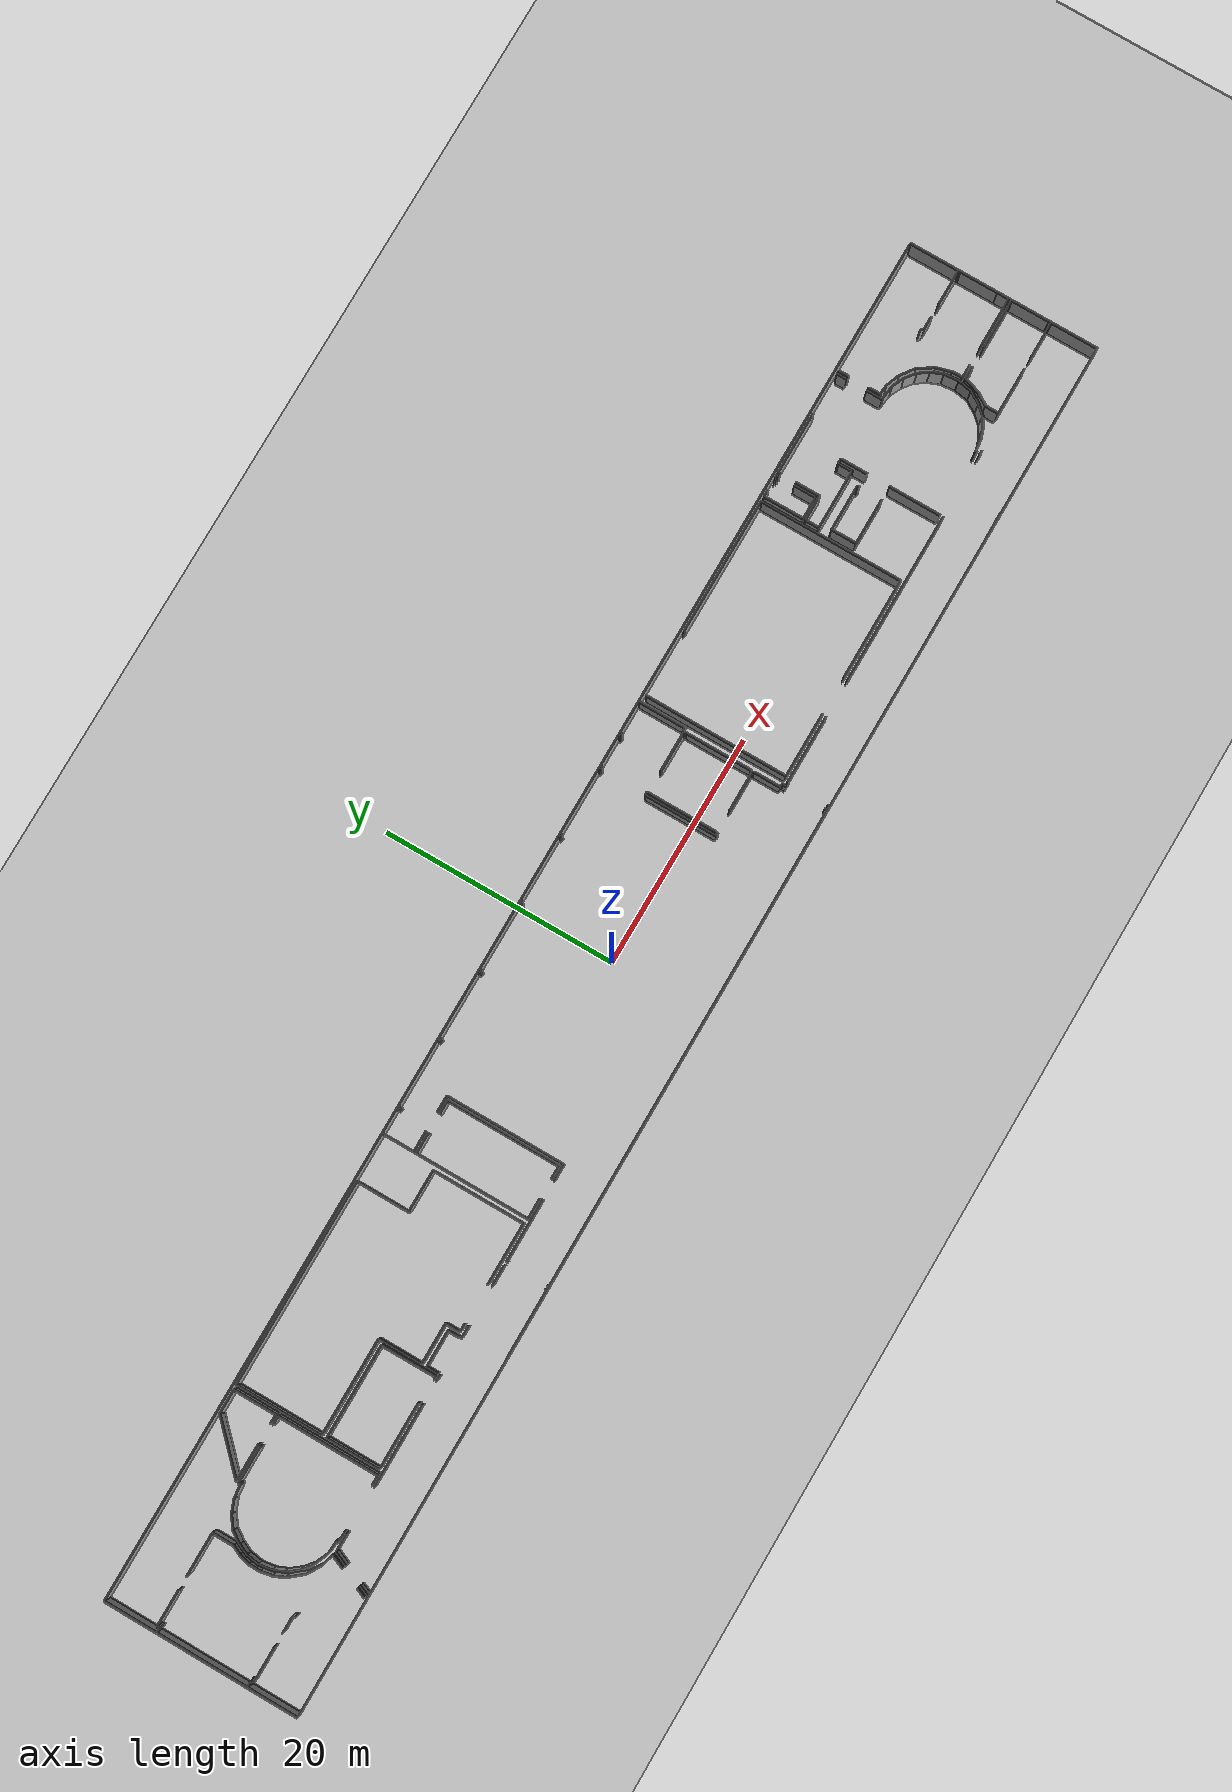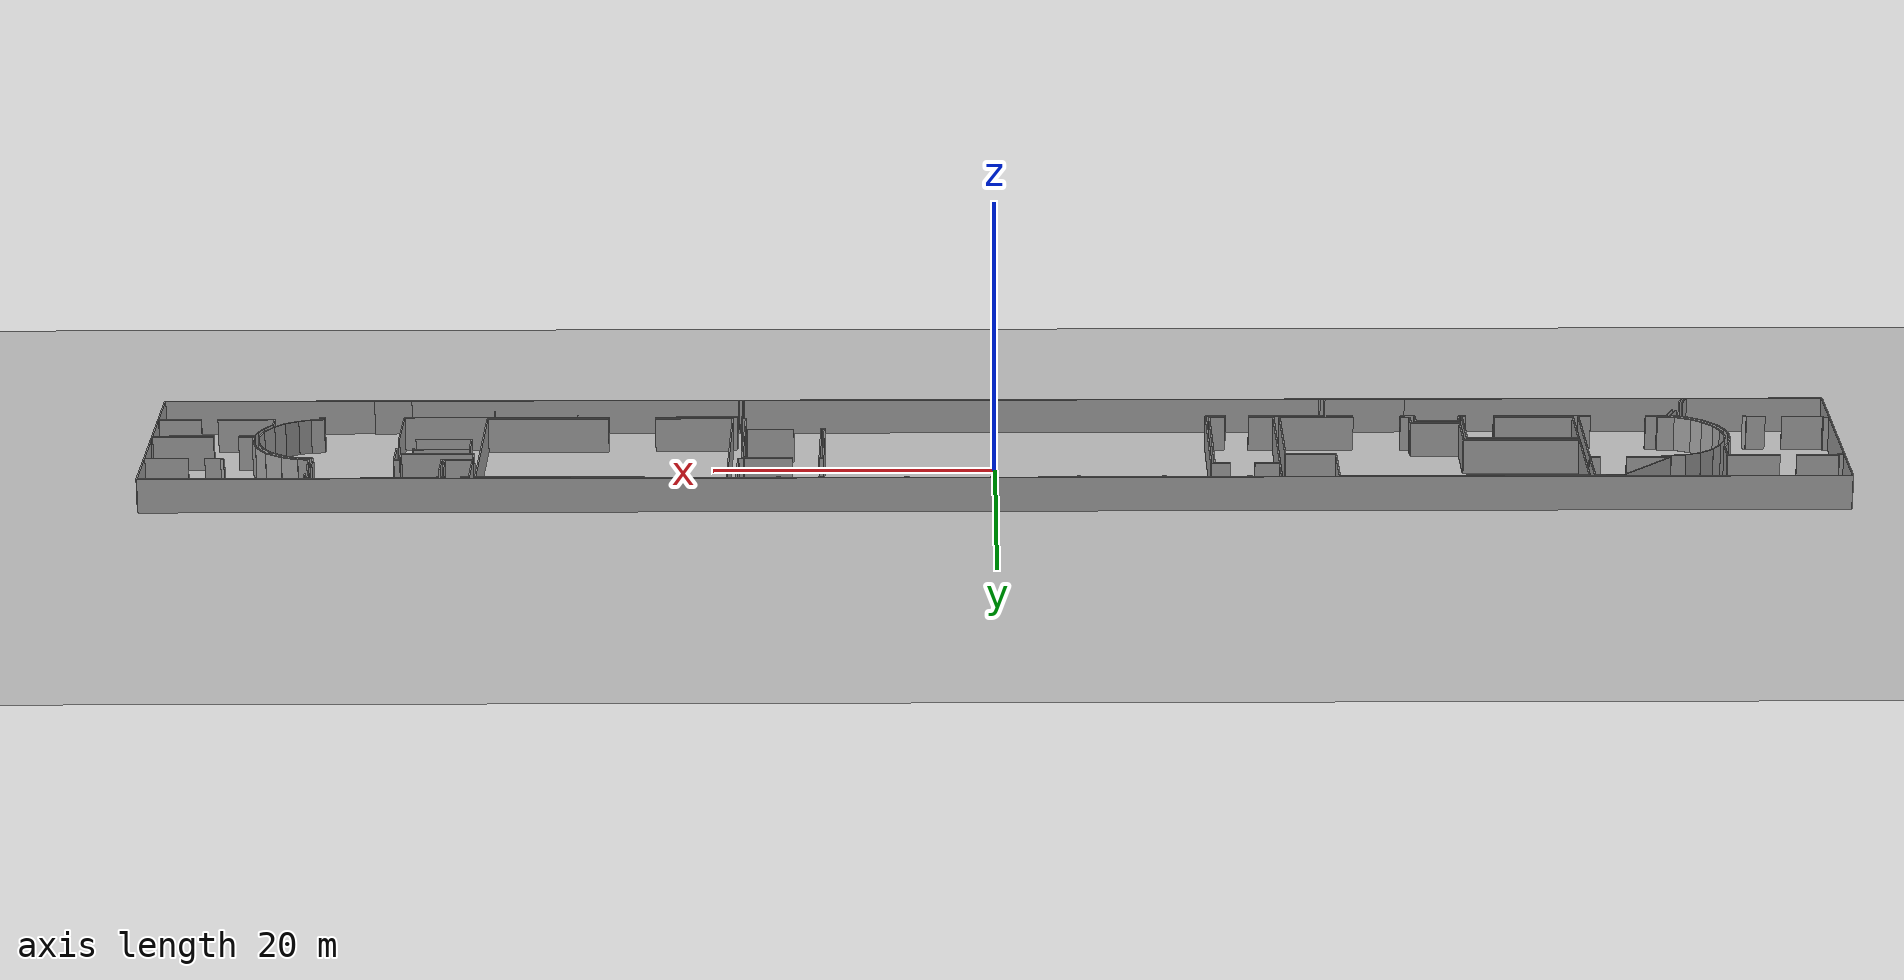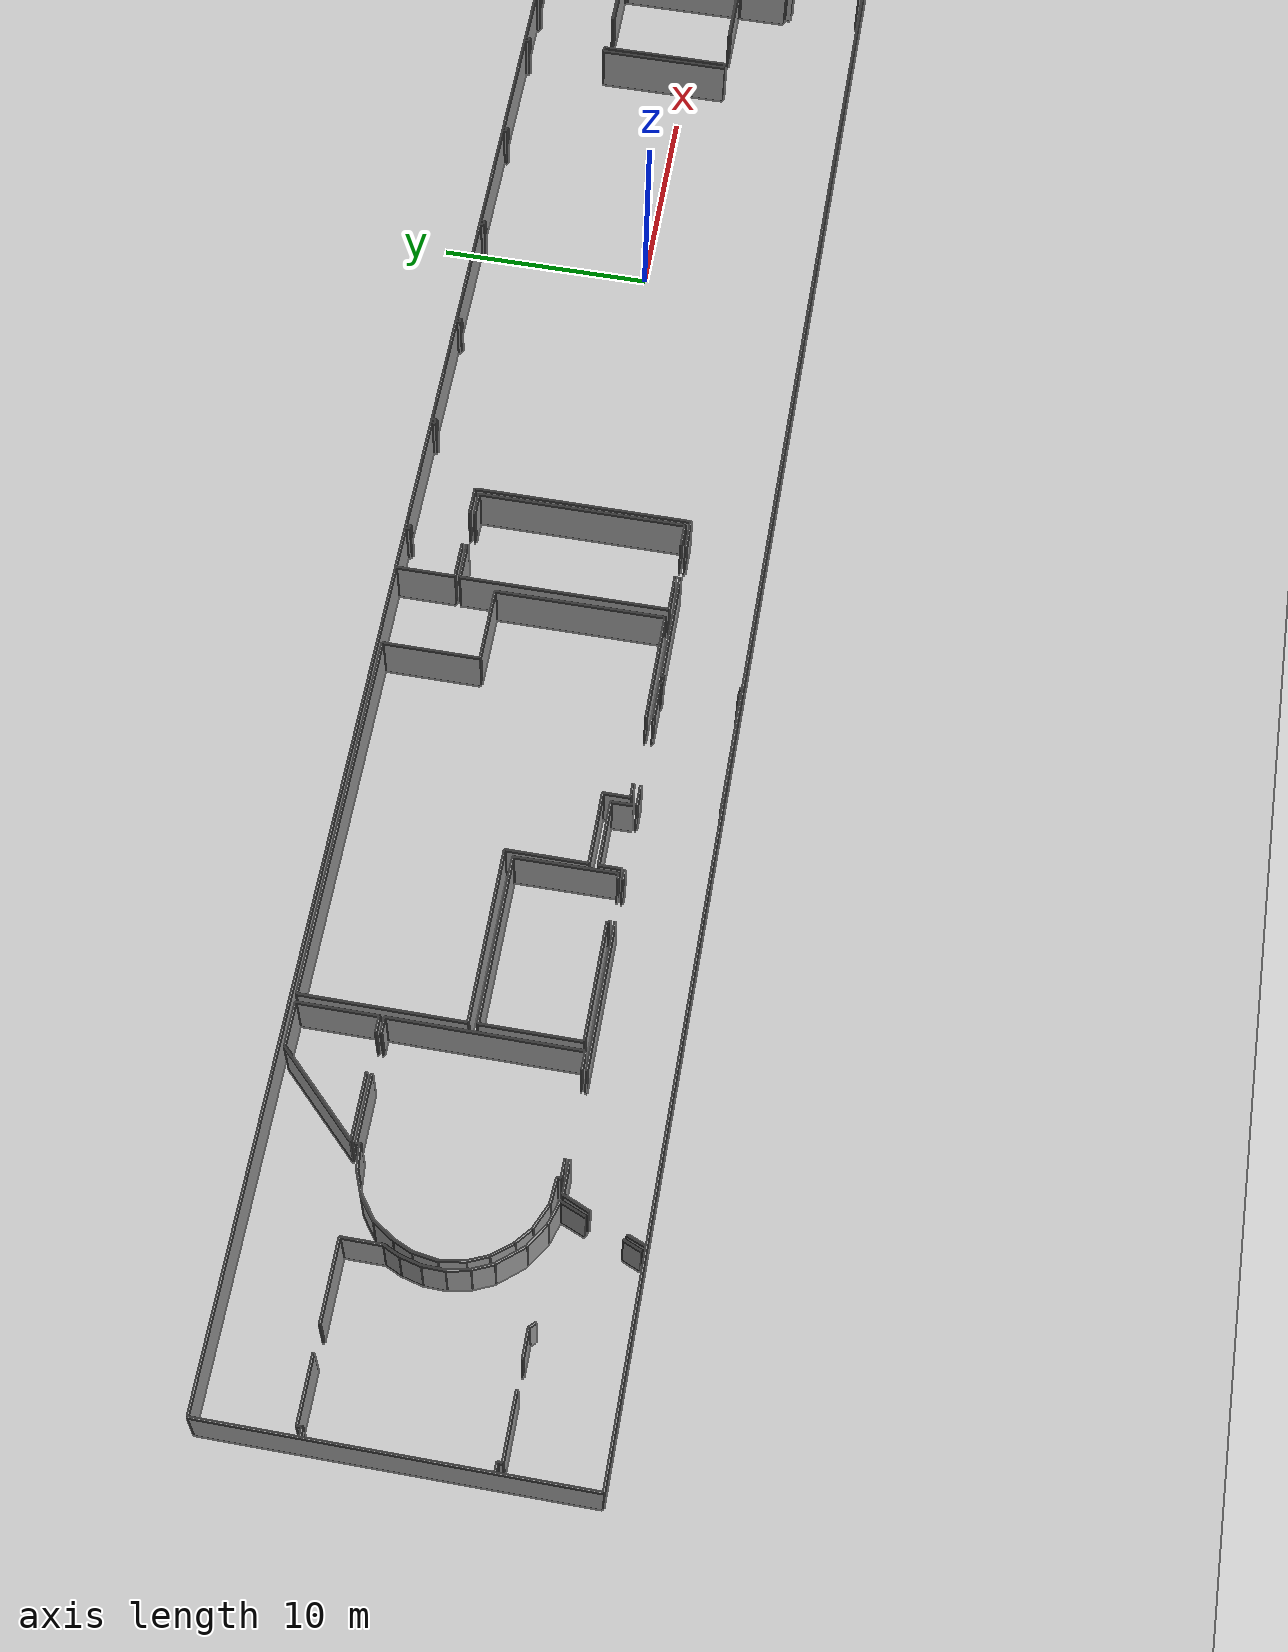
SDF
<sdf version="1.6">
  <world name="default">
    <light name="sun" type="directional">
      <cast_shadows>1</cast_shadows>
      <pose frame="">0 0 10 0 -0 0</pose>
      <diffuse>0.8 0.8 0.8 1</diffuse>
      <specular>0.1 0.1 0.1 1</specular>
      <attenuation>
        <range>1000</range>
        <constant>0.9</constant>
        <linear>0.01</linear>
        <quadratic>0.001</quadratic>
      </attenuation>
      <direction>-0.5 0.5 -1</direction>
    </light>
    <model name="ground_plane">
      <static>1</static>
      <link name="link">
        <collision name="collision">
          <geometry>
            <plane>
              <normal>0 0 1</normal>
              <size>100 100</size>
            </plane>
          </geometry>
          <surface>
            <friction>
              <ode>
                <mu>100</mu>
                <mu2>50</mu2>
              </ode>
              <torsional>
                <ode />
              </torsional>
            </friction>
            <contact>
              <ode />
            </contact>
            <bounce />
          </surface>
          <max_contacts>10</max_contacts>
        </collision>
        <visual name="visual">
          <cast_shadows>0</cast_shadows>
          <geometry>
            <plane>
              <normal>0 0 1</normal>
              <size>100 100</size>
            </plane>
          </geometry>
          <material>
            <script>
              <uri>file://media/materials/scripts/gazebo.material</uri>
              <name>Gazebo/Grey</name>
            </script>
          </material>
        </visual>
        <self_collide>0</self_collide>
        <kinematic>0</kinematic>
        <gravity>1</gravity>
      </link>
    </model>
    <gravity>0 0 -9.8</gravity>
    <magnetic_field>6e-06 2.3e-05 -4.2e-05</magnetic_field>
    <atmosphere type="adiabatic" />
    <physics default="0" name="default_physics" type="ode">
      <max_step_size>0.001</max_step_size>
      <real_time_factor>1</real_time_factor>
      <real_time_update_rate>1000</real_time_update_rate>
    </physics>
    <scene>
      <ambient>0.4 0.4 0.4 1</ambient>
      <background>0.7 0.7 0.7 1</background>
      <shadows>1</shadows>
    </scene>
    <spherical_coordinates>
      <surface_model>EARTH_WGS84</surface_model>
      <latitude_deg>0</latitude_deg>
      <longitude_deg>0</longitude_deg>
      <elevation>0</elevation>
      <heading_deg>0</heading_deg>
    </spherical_coordinates>
  <model name="50041186">
		<static>1</static>
		<link name="Wall_0">
			<collision name="Wall_0_Collision">
				<geometry>
					<box>
						<size>0.214501031255 0.1 2.5</size>
					</box>
				</geometry>
				<pose frame="">0.107250515627 0 1.25 0 0 0</pose>
			</collision>
			<visual name="Wall_0_Visual">
				<pose frame="">0.107250515627 0 1.25 0 0 0</pose>
				<geometry>
					<box>
						<size>0.214501031255 0.1 2.5</size>
					</box>
				</geometry>
				<material>
					<script>
						<uri>file://media/materials/scripts/gazebo.material</uri>
						<name>Gazebo/Grey</name>
					</script>
					<ambient>1 1 1 1</ambient>
				</material>
			</visual>
			<pose frame="">0.435348246867 -12.5315564017 0 0 0 1.57079632679</pose>
		</link>
		<link name="Wall_1">
			<collision name="Wall_1_Collision">
				<geometry>
					<box>
						<size>0.435348246867 0.1 2.5</size>
					</box>
				</geometry>
				<pose frame="">0.217674123433 0 1.25 0 0 0</pose>
			</collision>
			<visual name="Wall_1_Visual">
				<pose frame="">0.217674123433 0 1.25 0 0 0</pose>
				<geometry>
					<box>
						<size>0.435348246867 0.1 2.5</size>
					</box>
				</geometry>
				<material>
					<script>
						<uri>file://media/materials/scripts/gazebo.material</uri>
						<name>Gazebo/Grey</name>
					</script>
					<ambient>1 1 1 1</ambient>
				</material>
			</visual>
			<pose frame="">0.435348246867 -12.3170553705 0 0 0 3.14159265359</pose>
		</link>
		<link name="Wall_2">
			<collision name="Wall_2_Collision">
				<geometry>
					<box>
						<size>0.414786609551 0.1 2.5</size>
					</box>
				</geometry>
				<pose frame="">0.207393304776 0 1.25 0 0 0</pose>
			</collision>
			<visual name="Wall_2_Visual">
				<pose frame="">0.207393304776 0 1.25 0 0 0</pose>
				<geometry>
					<box>
						<size>0.414786609551 0.1 2.5</size>
					</box>
				</geometry>
				<material>
					<script>
						<uri>file://media/materials/scripts/gazebo.material</uri>
						<name>Gazebo/Grey</name>
					</script>
					<ambient>1 1 1 1</ambient>
				</material>
			</visual>
			<pose frame="">0.0 -4.5267333016 0 0 0 0.0</pose>
		</link>
		<link name="Wall_3">
			<collision name="Wall_3_Collision">
				<geometry>
					<box>
						<size>0.219831826115 0.1 2.5</size>
					</box>
				</geometry>
				<pose frame="">0.109915913057 0 1.25 0 0 0</pose>
			</collision>
			<visual name="Wall_3_Visual">
				<pose frame="">0.109915913057 0 1.25 0 0 0</pose>
				<geometry>
					<box>
						<size>0.219831826115 0.1 2.5</size>
					</box>
				</geometry>
				<material>
					<script>
						<uri>file://media/materials/scripts/gazebo.material</uri>
						<name>Gazebo/Grey</name>
					</script>
					<ambient>1 1 1 1</ambient>
				</material>
			</visual>
			<pose frame="">0.414786609551 -4.5267333016 0 0 0 1.57079632679</pose>
		</link>
		<link name="Wall_4">
			<collision name="Wall_4_Collision">
				<geometry>
					<box>
						<size>2.97623353958 0.1 2.5</size>
					</box>
				</geometry>
				<pose frame="">1.48811676979 0 1.25 0 0 0</pose>
			</collision>
			<visual name="Wall_4_Visual">
				<pose frame="">1.48811676979 0 1.25 0 0 0</pose>
				<geometry>
					<box>
						<size>2.97623353958 0.1 2.5</size>
					</box>
				</geometry>
				<material>
					<script>
						<uri>file://media/materials/scripts/gazebo.material</uri>
						<name>Gazebo/Grey</name>
					</script>
					<ambient>1 1 1 1</ambient>
				</material>
			</visual>
			<pose frame="">0.414786609551 -4.30690147549 0 0 0 0.0</pose>
		</link>
		<link name="Wall_5">
			<collision name="Wall_5_Collision">
				<geometry>
					<box>
						<size>3.70515627479 0.1 2.5</size>
					</box>
				</geometry>
				<pose frame="">1.85257813739 0 1.25 0 0 0</pose>
			</collision>
			<visual name="Wall_5_Visual">
				<pose frame="">1.85257813739 0 1.25 0 0 0</pose>
				<geometry>
					<box>
						<size>3.70515627479 0.1 2.5</size>
					</box>
				</geometry>
				<material>
					<script>
						<uri>file://media/materials/scripts/gazebo.material</uri>
						<name>Gazebo/Grey</name>
					</script>
					<ambient>1 1 1 1</ambient>
				</material>
			</visual>
			<pose frame="">4.55579882596 -4.30690147549 0 0 0 0.0</pose>
		</link>
		<link name="Wall_6">
			<collision name="Wall_6_Collision">
				<geometry>
					<box>
						<size>1.81983182611 0.1 2.5</size>
					</box>
				</geometry>
				<pose frame="">0.909915913057 0 1.25 0 0 0</pose>
			</collision>
			<visual name="Wall_6_Visual">
				<pose frame="">0.909915913057 0 1.25 0 0 0</pose>
				<geometry>
					<box>
						<size>1.81983182611 0.1 2.5</size>
					</box>
				</geometry>
				<material>
					<script>
						<uri>file://media/materials/scripts/gazebo.material</uri>
						<name>Gazebo/Grey</name>
					</script>
					<ambient>1 1 1 1</ambient>
				</material>
			</visual>
			<pose frame="">8.26095510075 -4.30690147549 0 0 0 -1.57079632679</pose>
		</link>
		<link name="Wall_7">
			<collision name="Wall_7_Collision">
				<geometry>
					<box>
						<size>0.802812789182 0.1 2.5</size>
					</box>
				</geometry>
				<pose frame="">0.401406394591 0 1.25 0 0 0</pose>
			</collision>
			<visual name="Wall_7_Visual">
				<pose frame="">0.401406394591 0 1.25 0 0 0</pose>
				<geometry>
					<box>
						<size>0.802812789182 0.1 2.5</size>
					</box>
				</geometry>
				<material>
					<script>
						<uri>file://media/materials/scripts/gazebo.material</uri>
						<name>Gazebo/Grey</name>
					</script>
					<ambient>1 1 1 1</ambient>
				</material>
			</visual>
			<pose frame="">8.26095510075 -6.1267333016 0 0 0 -1.99979208849</pose>
		</link>
		<link name="Wall_8">
			<collision name="Wall_8_Collision">
				<geometry>
					<box>
						<size>0.980194829963 0.1 2.5</size>
					</box>
				</geometry>
				<pose frame="">0.490097414981 0 1.25 0 0 0</pose>
			</collision>
			<visual name="Wall_8_Visual">
				<pose frame="">0.490097414981 0 1.25 0 0 0</pose>
				<geometry>
					<box>
						<size>0.980194829963 0.1 2.5</size>
					</box>
				</geometry>
				<material>
					<script>
						<uri>file://media/materials/scripts/gazebo.material</uri>
						<name>Gazebo/Grey</name>
					</script>
					<ambient>1 1 1 1</ambient>
				</material>
			</visual>
			<pose frame="">7.9270188799 -6.85679834999 0 0 0 -1.82164785353</pose>
		</link>
		<link name="Wall_9">
			<collision name="Wall_9_Collision">
				<geometry>
					<box>
						<size>1.00221968522 0.1 2.5</size>
					</box>
				</geometry>
				<pose frame="">0.50110984261 0 1.25 0 0 0</pose>
			</collision>
			<visual name="Wall_9_Visual">
				<pose frame="">0.50110984261 0 1.25 0 0 0</pose>
				<geometry>
					<box>
						<size>1.00221968522 0.1 2.5</size>
					</box>
				</geometry>
				<material>
					<script>
						<uri>file://media/materials/scripts/gazebo.material</uri>
						<name>Gazebo/Grey</name>
					</script>
					<ambient>1 1 1 1</ambient>
				</material>
			</visual>
			<pose frame="">7.68370617166 -7.80631445343 0 0 0 -1.59460738187</pose>
		</link>
		<link name="Wall_10">
			<collision name="Wall_10_Collision">
				<geometry>
					<box>
						<size>1.01922075863 0.1 2.5</size>
					</box>
				</geometry>
				<pose frame="">0.509610379313 0 1.25 0 0 0</pose>
			</collision>
			<visual name="Wall_10_Visual">
				<pose frame="">0.509610379313 0 1.25 0 0 0</pose>
				<geometry>
					<box>
						<size>1.01922075863 0.1 2.5</size>
					</box>
				</geometry>
				<material>
					<script>
						<uri>file://media/materials/scripts/gazebo.material</uri>
						<name>Gazebo/Grey</name>
					</script>
					<ambient>1 1 1 1</ambient>
				</material>
			</visual>
			<pose frame="">7.65984451848 -8.80825003966 0 0 0 -1.36333858213</pose>
		</link>
		<link name="Wall_11">
			<collision name="Wall_11_Collision">
				<geometry>
					<box>
						<size>0.984379025085 0.1 2.5</size>
					</box>
				</geometry>
				<pose frame="">0.492189512542 0 1.25 0 0 0</pose>
			</collision>
			<visual name="Wall_11_Visual">
				<pose frame="">0.492189512542 0 1.25 0 0 0</pose>
				<geometry>
					<box>
						<size>0.984379025085 0.1 2.5</size>
					</box>
				</geometry>
				<material>
					<script>
						<uri>file://media/materials/scripts/gazebo.material</uri>
						<name>Gazebo/Grey</name>
					</script>
					<ambient>1 1 1 1</ambient>
				</material>
			</visual>
			<pose frame="">7.869776297 -9.80561637316 0 0 0 -1.14619631937</pose>
		</link>
		<link name="Wall_12">
			<collision name="Wall_12_Collision">
				<geometry>
					<box>
						<size>1.47616845365 0.1 2.5</size>
					</box>
				</geometry>
				<pose frame="">0.738084226823 0 1.25 0 0 0</pose>
			</collision>
			<visual name="Wall_12_Visual">
				<pose frame="">0.738084226823 0 1.25 0 0 0</pose>
				<geometry>
					<box>
						<size>1.47616845365 0.1 2.5</size>
					</box>
				</geometry>
				<material>
					<script>
						<uri>file://media/materials/scripts/gazebo.material</uri>
						<name>Gazebo/Grey</name>
					</script>
					<ambient>1 1 1 1</ambient>
				</material>
			</visual>
			<pose frame="">8.27529747739 -10.7025860701 0 0 0 -0.876905731931</pose>
		</link>
		<link name="Wall_13">
			<collision name="Wall_13_Collision">
				<geometry>
					<box>
						<size>1.25161306481 0.1 2.5</size>
					</box>
				</geometry>
				<pose frame="">0.625806532405 0 1.25 0 0 0</pose>
			</collision>
			<visual name="Wall_13_Visual">
				<pose frame="">0.625806532405 0 1.25 0 0 0</pose>
				<geometry>
					<box>
						<size>1.25161306481 0.1 2.5</size>
					</box>
				</geometry>
				<material>
					<script>
						<uri>file://media/materials/scripts/gazebo.material</uri>
						<name>Gazebo/Grey</name>
					</script>
					<ambient>1 1 1 1</ambient>
				</material>
			</visual>
			<pose frame="">9.21935586229 -11.8374107568 0 0 0 -0.569832502966</pose>
		</link>
		<link name="Wall_14">
			<collision name="Wall_14_Collision">
				<geometry>
					<box>
						<size>1.13580694418 0.1 2.5</size>
					</box>
				</geometry>
				<pose frame="">0.567903472089 0 1.25 0 0 0</pose>
			</collision>
			<visual name="Wall_14_Visual">
				<pose frame="">0.567903472089 0 1.25 0 0 0</pose>
				<geometry>
					<box>
						<size>1.13580694418 0.1 2.5</size>
					</box>
				</geometry>
				<material>
					<script>
						<uri>file://media/materials/scripts/gazebo.material</uri>
						<name>Gazebo/Grey</name>
					</script>
					<ambient>1 1 1 1</ambient>
				</material>
			</visual>
			<pose frame="">10.2732032366 -12.5126447723 0 0 0 -0.298885076363</pose>
		</link>
		<link name="Wall_15">
			<collision name="Wall_15_Collision">
				<geometry>
					<box>
						<size>1.23903996177 0.1 2.5</size>
					</box>
				</geometry>
				<pose frame="">0.619519980884 0 1.25 0 0 0</pose>
			</collision>
			<visual name="Wall_15_Visual">
				<pose frame="">0.619519980884 0 1.25 0 0 0</pose>
				<geometry>
					<box>
						<size>1.23903996177 0.1 2.5</size>
					</box>
				</geometry>
				<material>
					<script>
						<uri>file://media/materials/scripts/gazebo.material</uri>
						<name>Gazebo/Grey</name>
					</script>
					<ambient>1 1 1 1</ambient>
				</material>
			</visual>
			<pose frame="">11.3586546089 -12.8470886879 0 0 0 -1.9669585284</pose>
		</link>
		<link name="Wall_16">
			<collision name="Wall_16_Collision">
				<geometry>
					<box>
						<size>0.882595050381 0.1 2.5</size>
					</box>
				</geometry>
				<pose frame="">0.441297525191 0 1.25 0 0 0</pose>
			</collision>
			<visual name="Wall_16_Visual">
				<pose frame="">0.441297525191 0 1.25 0 0 0</pose>
				<geometry>
					<box>
						<size>0.882595050381 0.1 2.5</size>
					</box>
				</geometry>
				<material>
					<script>
						<uri>file://media/materials/scripts/gazebo.material</uri>
						<name>Gazebo/Grey</name>
					</script>
					<ambient>1 1 1 1</ambient>
				</material>
			</visual>
			<pose frame="">10.2049182929 -15.6444867523 0 0 0 -1.97330887364</pose>
		</link>
		<link name="Wall_17">
			<collision name="Wall_17_Collision">
				<geometry>
					<box>
						<size>0.352043845135 0.1 2.5</size>
					</box>
				</geometry>
				<pose frame="">0.176021922568 0 1.25 0 0 0</pose>
			</collision>
			<visual name="Wall_17_Visual">
				<pose frame="">0.176021922568 0 1.25 0 0 0</pose>
				<geometry>
					<box>
						<size>0.352043845135 0.1 2.5</size>
					</box>
				</geometry>
				<material>
					<script>
						<uri>file://media/materials/scripts/gazebo.material</uri>
						<name>Gazebo/Grey</name>
					</script>
					<ambient>1 1 1 1</ambient>
				</material>
			</visual>
			<pose frame="">6.17788354752 -12.791876884 0 0 0 2.33936792952</pose>
		</link>
		<link name="Wall_18">
			<collision name="Wall_18_Collision">
				<geometry>
					<box>
						<size>1.33676027289 0.1 2.5</size>
					</box>
				</geometry>
				<pose frame="">0.668380136443 0 1.25 0 0 0</pose>
			</collision>
			<visual name="Wall_18_Visual">
				<pose frame="">0.668380136443 0 1.25 0 0 0</pose>
				<geometry>
					<box>
						<size>1.33676027289 0.1 2.5</size>
					</box>
				</geometry>
				<material>
					<script>
						<uri>file://media/materials/scripts/gazebo.material</uri>
						<name>Gazebo/Grey</name>
					</script>
					<ambient>1 1 1 1</ambient>
				</material>
			</visual>
			<pose frame="">5.93317467872 -12.5387910519 0 0 0 3.14159265359</pose>
		</link>
		<link name="Wall_19">
			<collision name="Wall_19_Collision">
				<geometry>
					<box>
						<size>2.96405769477 0.1 2.5</size>
					</box>
				</geometry>
				<pose frame="">1.48202884739 0 1.25 0 0 0</pose>
			</collision>
			<visual name="Wall_19_Visual">
				<pose frame="">1.48202884739 0 1.25 0 0 0</pose>
				<geometry>
					<box>
						<size>2.96405769477 0.1 2.5</size>
					</box>
				</geometry>
				<material>
					<script>
						<uri>file://media/materials/scripts/gazebo.material</uri>
						<name>Gazebo/Grey</name>
					</script>
					<ambient>1 1 1 1</ambient>
				</material>
			</visual>
			<pose frame="">3.39939711249 -12.5387910519 0 0 0 3.13915185854</pose>
		</link>
		<link name="Wall_20">
			<collision name="Wall_20_Collision">
				<geometry>
					<box>
						<size>5.79241630969 0.1 2.5</size>
					</box>
				</geometry>
				<pose frame="">2.89620815485 0 1.25 0 0 0</pose>
			</collision>
			<visual name="Wall_20_Visual">
				<pose frame="">2.89620815485 0 1.25 0 0 0</pose>
				<geometry>
					<box>
						<size>5.79241630969 0.1 2.5</size>
					</box>
				</geometry>
				<material>
					<script>
						<uri>file://media/materials/scripts/gazebo.material</uri>
						<name>Gazebo/Grey</name>
					</script>
					<ambient>1 1 1 1</ambient>
				</material>
			</visual>
			<pose frame="">36.0396001904 -16.5755989211 0 0 0 3.14159265359</pose>
		</link>
		<link name="Wall_21">
			<collision name="Wall_21_Collision">
				<geometry>
					<box>
						<size>0.890921661925 0.1 2.5</size>
					</box>
				</geometry>
				<pose frame="">0.445460830963 0 1.25 0 0 0</pose>
			</collision>
			<visual name="Wall_21_Visual">
				<pose frame="">0.445460830963 0 1.25 0 0 0</pose>
				<geometry>
					<box>
						<size>0.890921661925 0.1 2.5</size>
					</box>
				</geometry>
				<material>
					<script>
						<uri>file://media/materials/scripts/gazebo.material</uri>
						<name>Gazebo/Grey</name>
					</script>
					<ambient>1 1 1 1</ambient>
				</material>
			</visual>
			<pose frame="">10.0965254641 -16.5755989211 0 0 0 1.1859778071</pose>
		</link>
		<link name="Wall_22">
			<collision name="Wall_22_Collision">
				<geometry>
					<box>
						<size>1.31678040376 0.1 2.5</size>
					</box>
				</geometry>
				<pose frame="">0.658390201879 0 1.25 0 0 0</pose>
			</collision>
			<visual name="Wall_22_Visual">
				<pose frame="">0.658390201879 0 1.25 0 0 0</pose>
				<geometry>
					<box>
						<size>1.31678040376 0.1 2.5</size>
					</box>
				</geometry>
				<material>
					<script>
						<uri>file://media/materials/scripts/gazebo.material</uri>
						<name>Gazebo/Grey</name>
					</script>
					<ambient>1 1 1 1</ambient>
				</material>
			</visual>
			<pose frame="">11.1187688402 -14.1028716484 0 0 0 1.15652589971</pose>
		</link>
		<link name="Wall_23">
			<collision name="Wall_23_Collision">
				<geometry>
					<box>
						<size>1.53165528491 0.1 2.5</size>
					</box>
				</geometry>
				<pose frame="">0.765827642456 0 1.25 0 0 0</pose>
			</collision>
			<visual name="Wall_23_Visual">
				<pose frame="">0.765827642456 0 1.25 0 0 0</pose>
				<geometry>
					<box>
						<size>1.53165528491 0.1 2.5</size>
					</box>
				</geometry>
				<material>
					<script>
						<uri>file://media/materials/scripts/gazebo.material</uri>
						<name>Gazebo/Grey</name>
					</script>
					<ambient>1 1 1 1</ambient>
				</material>
			</visual>
			<pose frame="">11.6488021577 -12.8974773917 0 0 0 -0.00936410848774</pose>
		</link>
		<link name="Wall_24">
			<collision name="Wall_24_Collision">
				<geometry>
					<box>
						<size>6.98346818975 0.1 2.5</size>
					</box>
				</geometry>
				<pose frame="">3.49173409488 0 1.25 0 0 0</pose>
			</collision>
			<visual name="Wall_24_Visual">
				<pose frame="">3.49173409488 0 1.25 0 0 0</pose>
				<geometry>
					<box>
						<size>6.98346818975 0.1 2.5</size>
					</box>
				</geometry>
				<material>
					<script>
						<uri>file://media/materials/scripts/gazebo.material</uri>
						<name>Gazebo/Grey</name>
					</script>
					<ambient>1 1 1 1</ambient>
				</material>
			</visual>
			<pose frame="">17.1131207362 -12.9118197684 0 0 0 0.0</pose>
		</link>
		<link name="Wall_25">
			<collision name="Wall_25_Collision">
				<geometry>
					<box>
						<size>0.503125495796 0.1 2.5</size>
					</box>
				</geometry>
				<pose frame="">0.251562747898 0 1.25 0 0 0</pose>
			</collision>
			<visual name="Wall_25_Visual">
				<pose frame="">0.251562747898 0 1.25 0 0 0</pose>
				<geometry>
					<box>
						<size>0.503125495796 0.1 2.5</size>
					</box>
				</geometry>
				<material>
					<script>
						<uri>file://media/materials/scripts/gazebo.material</uri>
						<name>Gazebo/Grey</name>
					</script>
					<ambient>1 1 1 1</ambient>
				</material>
			</visual>
			<pose frame="">26.0928446771 -12.9118197684 0 0 0 0.0</pose>
		</link>
		<link name="Wall_26">
			<collision name="Wall_26_Collision">
				<geometry>
					<box>
						<size>1.02110106299 0.1 2.5</size>
					</box>
				</geometry>
				<pose frame="">0.510550531493 0 1.25 0 0 0</pose>
			</collision>
			<visual name="Wall_26_Visual">
				<pose frame="">0.510550531493 0 1.25 0 0 0</pose>
				<geometry>
					<box>
						<size>1.02110106299 0.1 2.5</size>
					</box>
				</geometry>
				<material>
					<script>
						<uri>file://media/materials/scripts/gazebo.material</uri>
						<name>Gazebo/Grey</name>
					</script>
					<ambient>1 1 1 1</ambient>
				</material>
			</visual>
			<pose frame="">29.7769316199 -12.9118197684 0 0 0 0.0</pose>
		</link>
		<link name="Wall_27">
			<collision name="Wall_27_Collision">
				<geometry>
					<box>
						<size>1.84572425829 0.1 2.5</size>
					</box>
				</geometry>
				<pose frame="">0.922862129145 0 1.25 0 0 0</pose>
			</collision>
			<visual name="Wall_27_Visual">
				<pose frame="">0.922862129145 0 1.25 0 0 0</pose>
				<geometry>
					<box>
						<size>1.84572425829 0.1 2.5</size>
					</box>
				</geometry>
				<material>
					<script>
						<uri>file://media/materials/scripts/gazebo.material</uri>
						<name>Gazebo/Grey</name>
					</script>
					<ambient>1 1 1 1</ambient>
				</material>
			</visual>
			<pose frame="">34.1938759321 -12.9118197684 0 0 0 0.0</pose>
		</link>
		<link name="Wall_28">
			<collision name="Wall_28_Collision">
				<geometry>
					<box>
						<size>0.11511978423 0.1 2.5</size>
					</box>
				</geometry>
				<pose frame="">0.0575598921149 0 1.25 0 0 0</pose>
			</collision>
			<visual name="Wall_28_Visual">
				<pose frame="">0.0575598921149 0 1.25 0 0 0</pose>
				<geometry>
					<box>
						<size>0.11511978423 0.1 2.5</size>
					</box>
				</geometry>
				<material>
					<script>
						<uri>file://media/materials/scripts/gazebo.material</uri>
						<name>Gazebo/Grey</name>
					</script>
					<ambient>1 1 1 1</ambient>
				</material>
			</visual>
			<pose frame="">36.0396001904 -12.9118197684 0 0 0 -1.57079632679</pose>
		</link>
		<link name="Wall_29">
			<collision name="Wall_29_Collision">
				<geometry>
					<box>
						<size>0.14253530065 0.1 2.5</size>
					</box>
				</geometry>
				<pose frame="">0.0712676503252 0 1.25 0 0 0</pose>
			</collision>
			<visual name="Wall_29_Visual">
				<pose frame="">0.0712676503252 0 1.25 0 0 0</pose>
				<geometry>
					<box>
						<size>0.14253530065 0.1 2.5</size>
					</box>
				</geometry>
				<material>
					<script>
						<uri>file://media/materials/scripts/gazebo.material</uri>
						<name>Gazebo/Grey</name>
					</script>
					<ambient>1 1 1 1</ambient>
				</material>
			</visual>
			<pose frame="">36.0396001904 -16.4330636205 0 0 0 -1.57079632679</pose>
		</link>
		<link name="Wall_30">
			<collision name="Wall_30_Collision">
				<geometry>
					<box>
						<size>0.87348881485 0.1 2.5</size>
					</box>
				</geometry>
				<pose frame="">0.436744407425 0 1.25 0 0 0</pose>
			</collision>
			<visual name="Wall_30_Visual">
				<pose frame="">0.436744407425 0 1.25 0 0 0</pose>
				<geometry>
					<box>
						<size>0.87348881485 0.1 2.5</size>
					</box>
				</geometry>
				<material>
					<script>
						<uri>file://media/materials/scripts/gazebo.material</uri>
						<name>Gazebo/Grey</name>
					</script>
					<ambient>1 1 1 1</ambient>
				</material>
			</visual>
			<pose frame="">18.0135173727 -12.7075995558 0 0 0 3.14159265359</pose>
		</link>
		<link name="Wall_31">
			<collision name="Wall_31_Collision">
				<geometry>
					<box>
						<size>0.841757893067 0.1 2.5</size>
					</box>
				</geometry>
				<pose frame="">0.420878946533 0 1.25 0 0 0</pose>
			</collision>
			<visual name="Wall_31_Visual">
				<pose frame="">0.420878946533 0 1.25 0 0 0</pose>
				<geometry>
					<box>
						<size>0.841757893067 0.1 2.5</size>
					</box>
				</geometry>
				<material>
					<script>
						<uri>file://media/materials/scripts/gazebo.material</uri>
						<name>Gazebo/Grey</name>
					</script>
					<ambient>1 1 1 1</ambient>
				</material>
			</visual>
			<pose frame="">13.1731556402 -12.7075995558 0 0 0 3.14159265359</pose>
		</link>
		<link name="Wall_32">
			<collision name="Wall_32_Collision">
				<geometry>
					<box>
						<size>0.181373948913 0.1 2.5</size>
					</box>
				</geometry>
				<pose frame="">0.0906869744566 0 1.25 0 0 0</pose>
			</collision>
			<visual name="Wall_32_Visual">
				<pose frame="">0.0906869744566 0 1.25 0 0 0</pose>
				<geometry>
					<box>
						<size>0.181373948913 0.1 2.5</size>
					</box>
				</geometry>
				<material>
					<script>
						<uri>file://media/materials/scripts/gazebo.material</uri>
						<name>Gazebo/Grey</name>
					</script>
					<ambient>1 1 1 1</ambient>
				</material>
			</visual>
			<pose frame="">12.3313977471 -12.7075995558 0 0 0 1.57079632679</pose>
		</link>
		<link name="Wall_33">
			<collision name="Wall_33_Collision">
				<geometry>
					<box>
						<size>1.19602337415 0.1 2.5</size>
					</box>
				</geometry>
				<pose frame="">0.598011687073 0 1.25 0 0 0</pose>
			</collision>
			<visual name="Wall_33_Visual">
				<pose frame="">0.598011687073 0 1.25 0 0 0</pose>
				<geometry>
					<box>
						<size>1.19602337415 0.1 2.5</size>
					</box>
				</geometry>
				<material>
					<script>
						<uri>file://media/materials/scripts/gazebo.material</uri>
						<name>Gazebo/Grey</name>
					</script>
					<ambient>1 1 1 1</ambient>
				</material>
			</visual>
			<pose frame="">12.3313977471 -12.5262256069 0 0 0 3.07298441104</pose>
		</link>
		<link name="Wall_34">
			<collision name="Wall_34_Collision">
				<geometry>
					<box>
						<size>1.2624915988 0.1 2.5</size>
					</box>
				</geometry>
				<pose frame="">0.631245799402 0 1.25 0 0 0</pose>
			</collision>
			<visual name="Wall_34_Visual">
				<pose frame="">0.631245799402 0 1.25 0 0 0</pose>
				<geometry>
					<box>
						<size>1.2624915988 0.1 2.5</size>
					</box>
				</geometry>
				<material>
					<script>
						<uri>file://media/materials/scripts/gazebo.material</uri>
						<name>Gazebo/Grey</name>
					</script>
					<ambient>1 1 1 1</ambient>
				</material>
			</visual>
			<pose frame="">11.1381881644 -12.444232905 0 0 0 2.72521592054</pose>
		</link>
		<link name="Wall_35">
			<collision name="Wall_35_Collision">
				<geometry>
					<box>
						<size>0.931648585218 0.1 2.5</size>
					</box>
				</geometry>
				<pose frame="">0.465824292609 0 1.25 0 0 0</pose>
			</collision>
			<visual name="Wall_35_Visual">
				<pose frame="">0.465824292609 0 1.25 0 0 0</pose>
				<geometry>
					<box>
						<size>0.931648585218 0.1 2.5</size>
					</box>
				</geometry>
				<material>
					<script>
						<uri>file://media/materials/scripts/gazebo.material</uri>
						<name>Gazebo/Grey</name>
					</script>
					<ambient>1 1 1 1</ambient>
				</material>
			</visual>
			<pose frame="">9.98356338252 -11.9336189116 0 0 0 2.44687182057</pose>
		</link>
		<link name="Wall_36">
			<collision name="Wall_36_Collision">
				<geometry>
					<box>
						<size>1.13881285767 0.1 2.5</size>
					</box>
				</geometry>
				<pose frame="">0.569406428836 0 1.25 0 0 0</pose>
			</collision>
			<visual name="Wall_36_Visual">
				<pose frame="">0.569406428836 0 1.25 0 0 0</pose>
				<geometry>
					<box>
						<size>1.13881285767 0.1 2.5</size>
					</box>
				</geometry>
				<material>
					<script>
						<uri>file://media/materials/scripts/gazebo.material</uri>
						<name>Gazebo/Grey</name>
					</script>
					<ambient>1 1 1 1</ambient>
				</material>
			</visual>
			<pose frame="">9.26784071077 -11.3372045058 0 0 0 2.23444943488</pose>
		</link>
		<link name="Wall_37">
			<collision name="Wall_37_Collision">
				<geometry>
					<box>
						<size>0.951009476274 0.1 2.5</size>
					</box>
				</geometry>
				<pose frame="">0.475504738137 0 1.25 0 0 0</pose>
			</collision>
			<visual name="Wall_37_Visual">
				<pose frame="">0.475504738137 0 1.25 0 0 0</pose>
				<geometry>
					<box>
						<size>0.951009476274 0.1 2.5</size>
					</box>
				</geometry>
				<material>
					<script>
						<uri>file://media/materials/scripts/gazebo.material</uri>
						<name>Gazebo/Grey</name>
					</script>
					<ambient>1 1 1 1</ambient>
				</material>
			</visual>
			<pose frame="">8.56633349199 -10.4401078851 0 0 0 1.9783693537</pose>
		</link>
		<link name="Wall_38">
			<collision name="Wall_38_Collision">
				<geometry>
					<box>
						<size>1.1499593763 0.1 2.5</size>
					</box>
				</geometry>
				<pose frame="">0.574979688152 0 1.25 0 0 0</pose>
			</collision>
			<visual name="Wall_38_Visual">
				<pose frame="">0.574979688152 0 1.25 0 0 0</pose>
				<geometry>
					<box>
						<size>1.1499593763 0.1 2.5</size>
					</box>
				</geometry>
				<material>
					<script>
						<uri>file://media/materials/scripts/gazebo.material</uri>
						<name>Gazebo/Grey</name>
					</script>
					<ambient>1 1 1 1</ambient>
				</material>
			</visual>
			<pose frame="">8.1893701412 -9.56699984135 0 0 0 1.72906795784</pose>
		</link>
		<link name="Wall_39">
			<collision name="Wall_39_Collision">
				<geometry>
					<box>
						<size>1.11420281715 0.1 2.5</size>
					</box>
				</geometry>
				<pose frame="">0.557101408577 0 1.25 0 0 0</pose>
			</collision>
			<visual name="Wall_39_Visual">
				<pose frame="">0.557101408577 0 1.25 0 0 0</pose>
				<geometry>
					<box>
						<size>1.11420281715 0.1 2.5</size>
					</box>
				</geometry>
				<material>
					<script>
						<uri>file://media/materials/scripts/gazebo.material</uri>
						<name>Gazebo/Grey</name>
					</script>
					<ambient>1 1 1 1</ambient>
				</material>
			</visual>
			<pose frame="">8.00812311598 -8.43141361257 0 0 0 1.42469457028</pose>
		</link>
		<link name="Wall_40">
			<collision name="Wall_40_Collision">
				<geometry>
					<box>
						<size>0.933560958273 0.1 2.5</size>
					</box>
				</geometry>
				<pose frame="">0.466780479137 0 1.25 0 0 0</pose>
			</collision>
			<visual name="Wall_40_Visual">
				<pose frame="">0.466780479137 0 1.25 0 0 0</pose>
				<geometry>
					<box>
						<size>0.933560958273 0.1 2.5</size>
					</box>
				</geometry>
				<material>
					<script>
						<uri>file://media/materials/scripts/gazebo.material</uri>
						<name>Gazebo/Grey</name>
					</script>
					<ambient>1 1 1 1</ambient>
				</material>
			</visual>
			<pose frame="">8.17033158813 -7.32908138981 0 0 0 1.15513959832</pose>
		</link>
		<link name="Wall_41">
			<collision name="Wall_41_Collision">
				<geometry>
					<box>
						<size>1.1434183312 0.1 2.5</size>
					</box>
				</geometry>
				<pose frame="">0.5717091656 0 1.25 0 0 0</pose>
			</collision>
			<visual name="Wall_41_Visual">
				<pose frame="">0.5717091656 0 1.25 0 0 0</pose>
				<geometry>
					<box>
						<size>1.1434183312 0.1 2.5</size>
					</box>
				</geometry>
				<material>
					<script>
						<uri>file://media/materials/scripts/gazebo.material</uri>
						<name>Gazebo/Grey</name>
					</script>
					<ambient>1 1 1 1</ambient>
				</material>
			</visual>
			<pose frame="">8.54729493892 -6.4750118991 0 0 0 0.987473347965</pose>
		</link>
		<link name="Wall_42">
			<collision name="Wall_42_Collision">
				<geometry>
					<box>
						<size>1.19290496616 0.1 2.5</size>
					</box>
				</geometry>
				<pose frame="">0.59645248308 0 1.25 0 0 0</pose>
			</collision>
			<visual name="Wall_42_Visual">
				<pose frame="">0.59645248308 0 1.25 0 0 0</pose>
				<geometry>
					<box>
						<size>1.19290496616 0.1 2.5</size>
					</box>
				</geometry>
				<material>
					<script>
						<uri>file://media/materials/scripts/gazebo.material</uri>
						<name>Gazebo/Grey</name>
					</script>
					<ambient>1 1 1 1</ambient>
				</material>
			</visual>
			<pose frame="">9.17709027447 -5.52067269554 0 0 0 0.643479829028</pose>
		</link>
		<link name="Wall_43">
			<collision name="Wall_43_Collision">
				<geometry>
					<box>
						<size>1.17057599085 0.1 2.5</size>
					</box>
				</geometry>
				<pose frame="">0.585287995426 0 1.25 0 0 0</pose>
			</collision>
			<visual name="Wall_43_Visual">
				<pose frame="">0.585287995426 0 1.25 0 0 0</pose>
				<geometry>
					<box>
						<size>1.17057599085 0.1 2.5</size>
					</box>
				</geometry>
				<material>
					<script>
						<uri>file://media/materials/scripts/gazebo.material</uri>
						<name>Gazebo/Grey</name>
					</script>
					<ambient>1 1 1 1</ambient>
				</material>
			</visual>
			<pose frame="">10.131429478 -4.8049500238 0 0 0 0.366854660876</pose>
		</link>
		<link name="Wall_44">
			<collision name="Wall_44_Collision">
				<geometry>
					<box>
						<size>1.09246250105 0.1 2.5</size>
					</box>
				</geometry>
				<pose frame="">0.546231250523 0 1.25 0 0 0</pose>
			</collision>
			<visual name="Wall_44_Visual">
				<pose frame="">0.546231250523 0 1.25 0 0 0</pose>
				<geometry>
					<box>
						<size>1.09246250105 0.1 2.5</size>
					</box>
				</geometry>
				<material>
					<script>
						<uri>file://media/materials/scripts/gazebo.material</uri>
						<name>Gazebo/Grey</name>
					</script>
					<ambient>1 1 1 1</ambient>
				</material>
			</visual>
			<pose frame="">11.2241155006 -4.38508646676 0 0 0 0.091795891761</pose>
		</link>
		<link name="Wall_45">
			<collision name="Wall_45_Collision">
				<geometry>
					<box>
						<size>0.176550848802 0.1 2.5</size>
					</box>
				</geometry>
				<pose frame="">0.0882754244011 0 1.25 0 0 0</pose>
			</collision>
			<visual name="Wall_45_Visual">
				<pose frame="">0.0882754244011 0 1.25 0 0 0</pose>
				<geometry>
					<box>
						<size>0.176550848802 0.1 2.5</size>
					</box>
				</geometry>
				<material>
					<script>
						<uri>file://media/materials/scripts/gazebo.material</uri>
						<name>Gazebo/Grey</name>
					</script>
					<ambient>1 1 1 1</ambient>
				</material>
			</visual>
			<pose frame="">12.311978423 -4.28494367761 0 0 0 1.57079632679</pose>
		</link>
		<link name="Wall_46">
			<collision name="Wall_46_Collision">
				<geometry>
					<box>
						<size>3.12321116928 0.1 2.5</size>
					</box>
				</geometry>
				<pose frame="">1.56160558464 0 1.25 0 0 0</pose>
			</collision>
			<visual name="Wall_46_Visual">
				<pose frame="">1.56160558464 0 1.25 0 0 0</pose>
				<geometry>
					<box>
						<size>3.12321116928 0.1 2.5</size>
					</box>
				</geometry>
				<material>
					<script>
						<uri>file://media/materials/scripts/gazebo.material</uri>
						<name>Gazebo/Grey</name>
					</script>
					<ambient>1 1 1 1</ambient>
				</material>
			</visual>
			<pose frame="">12.311978423 -4.10839282881 0 0 0 0.0</pose>
		</link>
		<link name="Wall_47">
			<collision name="Wall_47_Collision">
				<geometry>
					<box>
						<size>0.753926701571 0.1 2.5</size>
					</box>
				</geometry>
				<pose frame="">0.376963350785 0 1.25 0 0 0</pose>
			</collision>
			<visual name="Wall_47_Visual">
				<pose frame="">0.376963350785 0 1.25 0 0 0</pose>
				<geometry>
					<box>
						<size>0.753926701571 0.1 2.5</size>
					</box>
				</geometry>
				<material>
					<script>
						<uri>file://media/materials/scripts/gazebo.material</uri>
						<name>Gazebo/Grey</name>
					</script>
					<ambient>1 1 1 1</ambient>
				</material>
			</visual>
			<pose frame="">17.2600983659 -4.10839282881 0 0 0 0.0</pose>
		</link>
		<link name="Wall_48">
			<collision name="Wall_48_Collision">
				<geometry>
					<box>
						<size>8.59920674194 0.1 2.5</size>
					</box>
				</geometry>
				<pose frame="">4.29960337097 0 1.25 0 0 0</pose>
			</collision>
			<visual name="Wall_48_Visual">
				<pose frame="">4.29960337097 0 1.25 0 0 0</pose>
				<geometry>
					<box>
						<size>8.59920674194 0.1 2.5</size>
					</box>
				</geometry>
				<material>
					<script>
						<uri>file://media/materials/scripts/gazebo.material</uri>
						<name>Gazebo/Grey</name>
					</script>
					<ambient>1 1 1 1</ambient>
				</material>
			</visual>
			<pose frame="">18.0140250674 -4.10839282881 0 0 0 -1.57085536651</pose>
		</link>
		<link name="Wall_49">
			<collision name="Wall_49_Collision">
				<geometry>
					<box>
						<size>0.766238299223 0.1 2.5</size>
					</box>
				</geometry>
				<pose frame="">0.383119149611 0 1.25 0 0 0</pose>
			</collision>
			<visual name="Wall_49_Visual">
				<pose frame="">0.383119149611 0 1.25 0 0 0</pose>
				<geometry>
					<box>
						<size>0.766238299223 0.1 2.5</size>
					</box>
				</geometry>
				<material>
					<script>
						<uri>file://media/materials/scripts/gazebo.material</uri>
						<name>Gazebo/Grey</name>
					</script>
					<ambient>1 1 1 1</ambient>
				</material>
			</visual>
			<pose frame="">18.0224020308 -3.88640330002 0 0 0 3.14159265359</pose>
		</link>
		<link name="Wall_50">
			<collision name="Wall_50_Collision">
				<geometry>
					<box>
						<size>3.10239568459 0.1 2.5</size>
					</box>
				</geometry>
				<pose frame="">1.5511978423 0 1.25 0 0 0</pose>
			</collision>
			<visual name="Wall_50_Visual">
				<pose frame="">1.5511978423 0 1.25 0 0 0</pose>
				<geometry>
					<box>
						<size>3.10239568459 0.1 2.5</size>
					</box>
				</geometry>
				<material>
					<script>
						<uri>file://media/materials/scripts/gazebo.material</uri>
						<name>Gazebo/Grey</name>
					</script>
					<ambient>1 1 1 1</ambient>
				</material>
			</visual>
			<pose frame="">15.4528319848 -3.88640330002 0 0 0 3.14159265359</pose>
		</link>
		<link name="Wall_51">
			<collision name="Wall_51_Collision">
				<geometry>
					<box>
						<size>5.12652999993 0.1 2.5</size>
					</box>
				</geometry>
				<pose frame="">2.56326499996 0 1.25 0 0 0</pose>
			</collision>
			<visual name="Wall_51_Visual">
				<pose frame="">2.56326499996 0 1.25 0 0 0</pose>
				<geometry>
					<box>
						<size>5.12652999993 0.1 2.5</size>
					</box>
				</geometry>
				<material>
					<script>
						<uri>file://media/materials/scripts/gazebo.material</uri>
						<name>Gazebo/Grey</name>
					</script>
					<ambient>1 1 1 1</ambient>
				</material>
			</visual>
			<pose frame="">12.3504363002 -3.88640330002 0 0 0 0.785100549569</pose>
		</link>
		<link name="Wall_52">
			<collision name="Wall_52_Collision">
				<geometry>
					<box>
						<size>2.03750594955 0.1 2.5</size>
					</box>
				</geometry>
				<pose frame="">1.01875297477 0 1.25 0 0 0</pose>
			</collision>
			<visual name="Wall_52_Visual">
				<pose frame="">1.01875297477 0 1.25 0 0 0</pose>
				<geometry>
					<box>
						<size>2.03750594955 0.1 2.5</size>
					</box>
				</geometry>
				<material>
					<script>
						<uri>file://media/materials/scripts/gazebo.material</uri>
						<name>Gazebo/Grey</name>
					</script>
					<ambient>1 1 1 1</ambient>
				</material>
			</visual>
			<pose frame="">15.9765191179 -0.262478184991 0 0 0 0.0</pose>
		</link>
		<link name="Wall_53">
			<collision name="Wall_53_Collision">
				<geometry>
					<box>
						<size>3.62393479699 0.1 2.5</size>
					</box>
				</geometry>
				<pose frame="">1.81196739849 0 1.25 0 0 0</pose>
			</collision>
			<visual name="Wall_53_Visual">
				<pose frame="">1.81196739849 0 1.25 0 0 0</pose>
				<geometry>
					<box>
						<size>3.62393479699 0.1 2.5</size>
					</box>
				</geometry>
				<material>
					<script>
						<uri>file://media/materials/scripts/gazebo.material</uri>
						<name>Gazebo/Grey</name>
					</script>
					<ambient>1 1 1 1</ambient>
				</material>
			</visual>
			<pose frame="">18.0140250674 -0.262478184991 0 0 0 -1.56848475904</pose>
		</link>
		<link name="Wall_54">
			<collision name="Wall_54_Collision">
				<geometry>
					<box>
						<size>0.271362843091 0.1 2.5</size>
					</box>
				</geometry>
				<pose frame="">0.135681421545 0 1.25 0 0 0</pose>
			</collision>
			<visual name="Wall_54_Visual">
				<pose frame="">0.135681421545 0 1.25 0 0 0</pose>
				<geometry>
					<box>
						<size>0.271362843091 0.1 2.5</size>
					</box>
				</geometry>
				<material>
					<script>
						<uri>file://media/materials/scripts/gazebo.material</uri>
						<name>Gazebo/Grey</name>
					</script>
					<ambient>1 1 1 1</ambient>
				</material>
			</visual>
			<pose frame="">26.389846105 -12.6956687292 0 0 0 3.14159265359</pose>
		</link>
		<link name="Wall_55">
			<collision name="Wall_55_Collision">
				<geometry>
					<box>
						<size>0.0767888307155 0.1 2.5</size>
					</box>
				</geometry>
				<pose frame="">0.0383944153578 0 1.25 0 0 0</pose>
			</collision>
			<visual name="Wall_55_Visual">
				<pose frame="">0.0383944153578 0 1.25 0 0 0</pose>
				<geometry>
					<box>
						<size>0.0767888307155 0.1 2.5</size>
					</box>
				</geometry>
				<material>
					<script>
						<uri>file://media/materials/scripts/gazebo.material</uri>
						<name>Gazebo/Grey</name>
					</script>
					<ambient>1 1 1 1</ambient>
				</material>
			</visual>
			<pose frame="">24.0986197049 -12.6956687292 0 0 0 3.14159265359</pose>
		</link>
		<link name="Wall_56">
			<collision name="Wall_56_Collision">
				<geometry>
					<box>
						<size>0.118546723782 0.1 2.5</size>
					</box>
				</geometry>
				<pose frame="">0.0592733618912 0 1.25 0 0 0</pose>
			</collision>
			<visual name="Wall_56_Visual">
				<pose frame="">0.0592733618912 0 1.25 0 0 0</pose>
				<geometry>
					<box>
						<size>0.118546723782 0.1 2.5</size>
					</box>
				</geometry>
				<material>
					<script>
						<uri>file://media/materials/scripts/gazebo.material</uri>
						<name>Gazebo/Grey</name>
					</script>
					<ambient>1 1 1 1</ambient>
				</material>
			</visual>
			<pose frame="">24.0218308742 -12.6956687292 0 0 0 1.57079632679</pose>
		</link>
		<link name="Wall_57">
			<collision name="Wall_57_Collision">
				<geometry>
					<box>
						<size>5.60228462637 0.1 2.5</size>
					</box>
				</geometry>
				<pose frame="">2.80114231318 0 1.25 0 0 0</pose>
			</collision>
			<visual name="Wall_57_Visual">
				<pose frame="">2.80114231318 0 1.25 0 0 0</pose>
				<geometry>
					<box>
						<size>5.60228462637 0.1 2.5</size>
					</box>
				</geometry>
				<material>
					<script>
						<uri>file://media/materials/scripts/gazebo.material</uri>
						<name>Gazebo/Grey</name>
					</script>
					<ambient>1 1 1 1</ambient>
				</material>
			</visual>
			<pose frame="">24.0218308742 -12.5771220054 0 0 0 3.14159265359</pose>
		</link>
		<link name="Wall_58">
			<collision name="Wall_58_Collision">
				<geometry>
					<box>
						<size>4.54894494685 0.1 2.5</size>
					</box>
				</geometry>
				<pose frame="">2.27447247343 0 1.25 0 0 0</pose>
			</collision>
			<visual name="Wall_58_Visual">
				<pose frame="">2.27447247343 0 1.25 0 0 0</pose>
				<geometry>
					<box>
						<size>4.54894494685 0.1 2.5</size>
					</box>
				</geometry>
				<material>
					<script>
						<uri>file://media/materials/scripts/gazebo.material</uri>
						<name>Gazebo/Grey</name>
					</script>
					<ambient>1 1 1 1</ambient>
				</material>
			</visual>
			<pose frame="">18.4195462478 -12.5771220054 0 0 0 1.57079632679</pose>
		</link>
		<link name="Wall_59">
			<collision name="Wall_59_Collision">
				<geometry>
					<box>
						<size>7.7494526416 0.1 2.5</size>
					</box>
				</geometry>
				<pose frame="">3.8747263208 0 1.25 0 0 0</pose>
			</collision>
			<visual name="Wall_59_Visual">
				<pose frame="">3.8747263208 0 1.25 0 0 0</pose>
				<geometry>
					<box>
						<size>7.7494526416 0.1 2.5</size>
					</box>
				</geometry>
				<material>
					<script>
						<uri>file://media/materials/scripts/gazebo.material</uri>
						<name>Gazebo/Grey</name>
					</script>
					<ambient>1 1 1 1</ambient>
				</material>
			</visual>
			<pose frame="">18.4195462478 -8.02817705854 0 0 0 0.0</pose>
		</link>
		<link name="Wall_60">
			<collision name="Wall_60_Collision">
				<geometry>
					<box>
						<size>0.189243217515 0.1 2.5</size>
					</box>
				</geometry>
				<pose frame="">0.0946216087577 0 1.25 0 0 0</pose>
			</collision>
			<visual name="Wall_60_Visual">
				<pose frame="">0.0946216087577 0 1.25 0 0 0</pose>
				<geometry>
					<box>
						<size>0.189243217515 0.1 2.5</size>
					</box>
				</geometry>
				<material>
					<script>
						<uri>file://media/materials/scripts/gazebo.material</uri>
						<name>Gazebo/Grey</name>
					</script>
					<ambient>1 1 1 1</ambient>
				</material>
			</visual>
			<pose frame="">26.1689988894 -8.02817705854 0 0 0 0.0</pose>
		</link>
		<link name="Wall_61">
			<collision name="Wall_61_Collision">
				<geometry>
					<box>
						<size>4.66759866614 0.1 2.5</size>
					</box>
				</geometry>
				<pose frame="">2.33379933307 0 1.25 0 0 0</pose>
			</collision>
			<visual name="Wall_61_Visual">
				<pose frame="">2.33379933307 0 1.25 0 0 0</pose>
				<geometry>
					<box>
						<size>4.66759866614 0.1 2.5</size>
					</box>
				</geometry>
				<material>
					<script>
						<uri>file://media/materials/scripts/gazebo.material</uri>
						<name>Gazebo/Grey</name>
					</script>
					<ambient>1 1 1 1</ambient>
				</material>
			</visual>
			<pose frame="">26.3582421069 -8.02817705854 0 0 0 -1.564025342</pose>
		</link>
		<link name="Wall_62">
			<collision name="Wall_62_Collision">
				<geometry>
					<box>
						<size>1.00472790735 0.1 2.5</size>
					</box>
				</geometry>
				<pose frame="">0.502363953673 0 1.25 0 0 0</pose>
			</collision>
			<visual name="Wall_62_Visual">
				<pose frame="">0.502363953673 0 1.25 0 0 0</pose>
				<geometry>
					<box>
						<size>1.00472790735 0.1 2.5</size>
					</box>
				</geometry>
				<material>
					<script>
						<uri>file://media/materials/scripts/gazebo.material</uri>
						<name>Gazebo/Grey</name>
					</script>
					<ambient>1 1 1 1</ambient>
				</material>
			</visual>
			<pose frame="">26.6283357132 -12.7587498017 0 0 0 1.57079632679</pose>
		</link>
		<link name="Wall_63">
			<collision name="Wall_63_Collision">
				<geometry>
					<box>
						<size>3.13323814057 0.1 2.5</size>
					</box>
				</geometry>
				<pose frame="">1.56661907028 0 1.25 0 0 0</pose>
			</collision>
			<visual name="Wall_63_Visual">
				<pose frame="">1.56661907028 0 1.25 0 0 0</pose>
				<geometry>
					<box>
						<size>3.13323814057 0.1 2.5</size>
					</box>
				</geometry>
				<material>
					<script>
						<uri>file://media/materials/scripts/gazebo.material</uri>
						<name>Gazebo/Grey</name>
					</script>
					<ambient>1 1 1 1</ambient>
				</material>
			</visual>
			<pose frame="">26.6283357132 -11.7540218943 0 0 0 0.0</pose>
		</link>
		<link name="Wall_64">
			<collision name="Wall_64_Collision">
				<geometry>
					<box>
						<size>1.00487184863 0.1 2.5</size>
					</box>
				</geometry>
				<pose frame="">0.502435924317 0 1.25 0 0 0</pose>
			</collision>
			<visual name="Wall_64_Visual">
				<pose frame="">0.502435924317 0 1.25 0 0 0</pose>
				<geometry>
					<box>
						<size>1.00487184863 0.1 2.5</size>
					</box>
				</geometry>
				<material>
					<script>
						<uri>file://media/materials/scripts/gazebo.material</uri>
						<name>Gazebo/Grey</name>
					</script>
					<ambient>1 1 1 1</ambient>
				</material>
			</visual>
			<pose frame="">29.7615738537 -11.7540218943 0 0 0 -1.55387020211</pose>
		</link>
		<link name="Wall_65">
			<collision name="Wall_65_Collision">
				<geometry>
					<box>
						<size>5.28269078217 0.1 2.5</size>
					</box>
				</geometry>
				<pose frame="">2.64134539108 0 1.25 0 0 0</pose>
			</collision>
			<visual name="Wall_65_Visual">
				<pose frame="">2.64134539108 0 1.25 0 0 0</pose>
				<geometry>
					<box>
						<size>5.28269078217 0.1 2.5</size>
					</box>
				</geometry>
				<material>
					<script>
						<uri>file://media/materials/scripts/gazebo.material</uri>
						<name>Gazebo/Grey</name>
					</script>
					<ambient>1 1 1 1</ambient>
				</material>
			</visual>
			<pose frame="">39.468951293 -12.5740758369 0 0 0 3.14159265359</pose>
		</link>
		<link name="Wall_66">
			<collision name="Wall_66_Collision">
				<geometry>
					<box>
						<size>0.673203236554 0.1 2.5</size>
					</box>
				</geometry>
				<pose frame="">0.336601618277 0 1.25 0 0 0</pose>
			</collision>
			<visual name="Wall_66_Visual">
				<pose frame="">0.336601618277 0 1.25 0 0 0</pose>
				<geometry>
					<box>
						<size>0.673203236554 0.1 2.5</size>
					</box>
				</geometry>
				<material>
					<script>
						<uri>file://media/materials/scripts/gazebo.material</uri>
						<name>Gazebo/Grey</name>
					</script>
					<ambient>1 1 1 1</ambient>
				</material>
			</visual>
			<pose frame="">30.8055211804 -12.5740758369 0 0 0 3.14159265359</pose>
		</link>
		<link name="Wall_67">
			<collision name="Wall_67_Collision">
				<geometry>
					<box>
						<size>1.24626368396 0.1 2.5</size>
					</box>
				</geometry>
				<pose frame="">0.62313184198 0 1.25 0 0 0</pose>
			</collision>
			<visual name="Wall_67_Visual">
				<pose frame="">0.62313184198 0 1.25 0 0 0</pose>
				<geometry>
					<box>
						<size>1.24626368396 0.1 2.5</size>
					</box>
				</geometry>
				<material>
					<script>
						<uri>file://media/materials/scripts/gazebo.material</uri>
						<name>Gazebo/Grey</name>
					</script>
					<ambient>1 1 1 1</ambient>
				</material>
			</visual>
			<pose frame="">30.1323179438 -12.5740758369 0 0 0 1.57079632679</pose>
		</link>
		<link name="Wall_68">
			<collision name="Wall_68_Collision">
				<geometry>
					<box>
						<size>3.49763604633 0.1 2.5</size>
					</box>
				</geometry>
				<pose frame="">1.74881802316 0 1.25 0 0 0</pose>
			</collision>
			<visual name="Wall_68_Visual">
				<pose frame="">1.74881802316 0 1.25 0 0 0</pose>
				<geometry>
					<box>
						<size>3.49763604633 0.1 2.5</size>
					</box>
				</geometry>
				<material>
					<script>
						<uri>file://media/materials/scripts/gazebo.material</uri>
						<name>Gazebo/Grey</name>
					</script>
					<ambient>1 1 1 1</ambient>
				</material>
			</visual>
			<pose frame="">30.1323179438 -11.3278121529 0 0 0 3.14159265359</pose>
		</link>
		<link name="Wall_69">
			<collision name="Wall_69_Collision">
				<geometry>
					<box>
						<size>3.71924480406 0.1 2.5</size>
					</box>
				</geometry>
				<pose frame="">1.85962240203 0 1.25 0 0 0</pose>
			</collision>
			<visual name="Wall_69_Visual">
				<pose frame="">1.85962240203 0 1.25 0 0 0</pose>
				<geometry>
					<box>
						<size>3.71924480406 0.1 2.5</size>
					</box>
				</geometry>
				<material>
					<script>
						<uri>file://media/materials/scripts/gazebo.material</uri>
						<name>Gazebo/Grey</name>
					</script>
					<ambient>1 1 1 1</ambient>
				</material>
			</visual>
			<pose frame="">26.6346818975 -11.3278121529 0 0 0 1.57079632679</pose>
		</link>
		<link name="Wall_70">
			<collision name="Wall_70_Collision">
				<geometry>
					<box>
						<size>8.23950499762 0.1 2.5</size>
					</box>
				</geometry>
				<pose frame="">4.11975249881 0 1.25 0 0 0</pose>
			</collision>
			<visual name="Wall_70_Visual">
				<pose frame="">4.11975249881 0 1.25 0 0 0</pose>
				<geometry>
					<box>
						<size>8.23950499762 0.1 2.5</size>
					</box>
				</geometry>
				<material>
					<script>
						<uri>file://media/materials/scripts/gazebo.material</uri>
						<name>Gazebo/Grey</name>
					</script>
					<ambient>1 1 1 1</ambient>
				</material>
			</visual>
			<pose frame="">26.6346818975 -7.60856734888 0 0 0 3.14159265359</pose>
		</link>
		<link name="Wall_71">
			<collision name="Wall_71_Collision">
				<geometry>
					<box>
						<size>7.38391242266 0.1 2.5</size>
					</box>
				</geometry>
				<pose frame="">3.69195621133 0 1.25 0 0 0</pose>
			</collision>
			<visual name="Wall_71_Visual">
				<pose frame="">3.69195621133 0 1.25 0 0 0</pose>
				<geometry>
					<box>
						<size>7.38391242266 0.1 2.5</size>
					</box>
				</geometry>
				<material>
					<script>
						<uri>file://media/materials/scripts/gazebo.material</uri>
						<name>Gazebo/Grey</name>
					</script>
					<ambient>1 1 1 1</ambient>
				</material>
			</visual>
			<pose frame="">18.3951768999 -7.60856734888 0 0 0 1.57079632679</pose>
		</link>
		<link name="Wall_72">
			<collision name="Wall_72_Collision">
				<geometry>
					<box>
						<size>17.4773917182 0.1 2.5</size>
					</box>
				</geometry>
				<pose frame="">8.73869585911 0 1.25 0 0 0</pose>
			</collision>
			<visual name="Wall_72_Visual">
				<pose frame="">8.73869585911 0 1.25 0 0 0</pose>
				<geometry>
					<box>
						<size>17.4773917182 0.1 2.5</size>
					</box>
				</geometry>
				<material>
					<script>
						<uri>file://media/materials/scripts/gazebo.material</uri>
						<name>Gazebo/Grey</name>
					</script>
					<ambient>1 1 1 1</ambient>
				</material>
			</visual>
			<pose frame="">18.3951768999 -0.224654926226 0 0 0 0.0</pose>
		</link>
		<link name="Wall_73">
			<collision name="Wall_73_Collision">
				<geometry>
					<box>
						<size>4.4942408377 0.1 2.5</size>
					</box>
				</geometry>
				<pose frame="">2.24712041885 0 1.25 0 0 0</pose>
			</collision>
			<visual name="Wall_73_Visual">
				<pose frame="">2.24712041885 0 1.25 0 0 0</pose>
				<geometry>
					<box>
						<size>4.4942408377 0.1 2.5</size>
					</box>
				</geometry>
				<material>
					<script>
						<uri>file://media/materials/scripts/gazebo.material</uri>
						<name>Gazebo/Grey</name>
					</script>
					<ambient>1 1 1 1</ambient>
				</material>
			</visual>
			<pose frame="">35.8725686181 -0.224654926226 0 0 0 -1.57079632679</pose>
		</link>
		<link name="Wall_74">
			<collision name="Wall_74_Collision">
				<geometry>
					<box>
						<size>3.57924797715 0.1 2.5</size>
					</box>
				</geometry>
				<pose frame="">1.78962398858 0 1.25 0 0 0</pose>
			</collision>
			<visual name="Wall_74_Visual">
				<pose frame="">1.78962398858 0 1.25 0 0 0</pose>
				<geometry>
					<box>
						<size>3.57924797715 0.1 2.5</size>
					</box>
				</geometry>
				<material>
					<script>
						<uri>file://media/materials/scripts/gazebo.material</uri>
						<name>Gazebo/Grey</name>
					</script>
					<ambient>1 1 1 1</ambient>
				</material>
			</visual>
			<pose frame="">35.8725686181 -4.71889576392 0 0 0 0.0</pose>
		</link>
		<link name="Wall_75">
			<collision name="Wall_75_Collision">
				<geometry>
					<box>
						<size>7.85519876113 0.1 2.5</size>
					</box>
				</geometry>
				<pose frame="">3.92759938056 0 1.25 0 0 0</pose>
			</collision>
			<visual name="Wall_75_Visual">
				<pose frame="">3.92759938056 0 1.25 0 0 0</pose>
				<geometry>
					<box>
						<size>7.85519876113 0.1 2.5</size>
					</box>
				</geometry>
				<material>
					<script>
						<uri>file://media/materials/scripts/gazebo.material</uri>
						<name>Gazebo/Grey</name>
					</script>
					<ambient>1 1 1 1</ambient>
				</material>
			</visual>
			<pose frame="">39.4518165953 -4.71889576392 0 0 0 -1.56861500563</pose>
		</link>
		<link name="Wall_76">
			<collision name="Wall_76_Collision">
				<geometry>
					<box>
						<size>1.1313977471 0.1 2.5</size>
					</box>
				</geometry>
				<pose frame="">0.565698873552 0 1.25 0 0 0</pose>
			</collision>
			<visual name="Wall_76_Visual">
				<pose frame="">0.565698873552 0 1.25 0 0 0</pose>
				<geometry>
					<box>
						<size>1.1313977471 0.1 2.5</size>
					</box>
				</geometry>
				<material>
					<script>
						<uri>file://media/materials/scripts/gazebo.material</uri>
						<name>Gazebo/Grey</name>
					</script>
					<ambient>1 1 1 1</ambient>
				</material>
			</visual>
			<pose frame="">44.5178486435 -12.6825955894 0 0 0 3.14159265359</pose>
		</link>
		<link name="Wall_77">
			<collision name="Wall_77_Collision">
				<geometry>
					<box>
						<size>1.79241630969 0.1 2.5</size>
					</box>
				</geometry>
				<pose frame="">0.896208154847 0 1.25 0 0 0</pose>
			</collision>
			<visual name="Wall_77_Visual">
				<pose frame="">0.896208154847 0 1.25 0 0 0</pose>
				<geometry>
					<box>
						<size>1.79241630969 0.1 2.5</size>
					</box>
				</geometry>
				<material>
					<script>
						<uri>file://media/materials/scripts/gazebo.material</uri>
						<name>Gazebo/Grey</name>
					</script>
					<ambient>1 1 1 1</ambient>
				</material>
			</visual>
			<pose frame="">41.7072505156 -12.6825955894 0 0 0 3.14159265359</pose>
		</link>
		<link name="Wall_78">
			<collision name="Wall_78_Collision">
				<geometry>
					<box>
						<size>9.69227352055 0.1 2.5</size>
					</box>
				</geometry>
				<pose frame="">4.84613676027 0 1.25 0 0 0</pose>
			</collision>
			<visual name="Wall_78_Visual">
				<pose frame="">4.84613676027 0 1.25 0 0 0</pose>
				<geometry>
					<box>
						<size>9.69227352055 0.1 2.5</size>
					</box>
				</geometry>
				<material>
					<script>
						<uri>file://media/materials/scripts/gazebo.material</uri>
						<name>Gazebo/Grey</name>
					</script>
					<ambient>1 1 1 1</ambient>
				</material>
			</visual>
			<pose frame="">39.9148342059 -12.6825955894 0 0 0 1.57079632679</pose>
		</link>
		<link name="Wall_79">
			<collision name="Wall_79_Collision">
				<geometry>
					<box>
						<size>1.77769316199 0.1 2.5</size>
					</box>
				</geometry>
				<pose frame="">0.888846580993 0 1.25 0 0 0</pose>
			</collision>
			<visual name="Wall_79_Visual">
				<pose frame="">0.888846580993 0 1.25 0 0 0</pose>
				<geometry>
					<box>
						<size>1.77769316199 0.1 2.5</size>
					</box>
				</geometry>
				<material>
					<script>
						<uri>file://media/materials/scripts/gazebo.material</uri>
						<name>Gazebo/Grey</name>
					</script>
					<ambient>1 1 1 1</ambient>
				</material>
			</visual>
			<pose frame="">39.9148342059 -2.99032206886 0 0 0 0.0</pose>
		</link>
		<link name="Wall_80">
			<collision name="Wall_80_Collision">
				<geometry>
					<box>
						<size>1.13850547358 0.1 2.5</size>
					</box>
				</geometry>
				<pose frame="">0.569252736792 0 1.25 0 0 0</pose>
			</collision>
			<visual name="Wall_80_Visual">
				<pose frame="">0.569252736792 0 1.25 0 0 0</pose>
				<geometry>
					<box>
						<size>1.13850547358 0.1 2.5</size>
					</box>
				</geometry>
				<material>
					<script>
						<uri>file://media/materials/scripts/gazebo.material</uri>
						<name>Gazebo/Grey</name>
					</script>
					<ambient>1 1 1 1</ambient>
				</material>
			</visual>
			<pose frame="">43.3750277646 -2.99032206886 0 0 0 0.0</pose>
		</link>
		<link name="Wall_81">
			<collision name="Wall_81_Collision">
				<geometry>
					<box>
						<size>9.69227448125 0.1 2.5</size>
					</box>
				</geometry>
				<pose frame="">4.84613724062 0 1.25 0 0 0</pose>
			</collision>
			<visual name="Wall_81_Visual">
				<pose frame="">4.84613724062 0 1.25 0 0 0</pose>
				<geometry>
					<box>
						<size>9.69227448125 0.1 2.5</size>
					</box>
				</geometry>
				<material>
					<script>
						<uri>file://media/materials/scripts/gazebo.material</uri>
						<name>Gazebo/Grey</name>
					</script>
					<ambient>1 1 1 1</ambient>
				</material>
			</visual>
			<pose frame="">44.5135332381 -2.99032206886 0 0 0 -1.57035108502</pose>
		</link>
		<link name="Wall_82">
			<collision name="Wall_82_Collision">
				<geometry>
					<box>
						<size>41.6785657623 0.1 2.5</size>
					</box>
				</geometry>
				<pose frame="">20.8392828812 0 1.25 0 0 0</pose>
			</collision>
			<visual name="Wall_82_Visual">
				<pose frame="">20.8392828812 0 1.25 0 0 0</pose>
				<geometry>
					<box>
						<size>41.6785657623 0.1 2.5</size>
					</box>
				</geometry>
				<material>
					<script>
						<uri>file://media/materials/scripts/gazebo.material</uri>
						<name>Gazebo/Grey</name>
					</script>
					<ambient>1 1 1 1</ambient>
				</material>
			</visual>
			<pose frame="">78.0665714739 -16.5882912899 0 0 0 3.14159265359</pose>
		</link>
		<link name="Wall_83">
			<collision name="Wall_83_Collision">
				<geometry>
					<box>
						<size>0.136062192607 0.1 2.5</size>
					</box>
				</geometry>
				<pose frame="">0.0680310963034 0 1.25 0 0 0</pose>
			</collision>
			<visual name="Wall_83_Visual">
				<pose frame="">0.0680310963034 0 1.25 0 0 0</pose>
				<geometry>
					<box>
						<size>0.136062192607 0.1 2.5</size>
					</box>
				</geometry>
				<material>
					<script>
						<uri>file://media/materials/scripts/gazebo.material</uri>
						<name>Gazebo/Grey</name>
					</script>
					<ambient>1 1 1 1</ambient>
				</material>
			</visual>
			<pose frame="">36.3880057116 -16.5882912899 0 0 0 1.57079632679</pose>
		</link>
		<link name="Wall_84">
			<collision name="Wall_84_Collision">
				<geometry>
					<box>
						<size>0.121465968586 0.1 2.5</size>
					</box>
				</geometry>
				<pose frame="">0.0607329842932 0 1.25 0 0 0</pose>
			</collision>
			<visual name="Wall_84_Visual">
				<pose frame="">0.0607329842932 0 1.25 0 0 0</pose>
				<geometry>
					<box>
						<size>0.121465968586 0.1 2.5</size>
					</box>
				</geometry>
				<material>
					<script>
						<uri>file://media/materials/scripts/gazebo.material</uri>
						<name>Gazebo/Grey</name>
					</script>
					<ambient>1 1 1 1</ambient>
				</material>
			</visual>
			<pose frame="">36.3880057116 -13.0384896081 0 0 0 1.57079632679</pose>
		</link>
		<link name="Wall_85">
			<collision name="Wall_85_Collision">
				<geometry>
					<box>
						<size>5.31074091702 0.1 2.5</size>
					</box>
				</geometry>
				<pose frame="">2.65537045851 0 1.25 0 0 0</pose>
			</collision>
			<visual name="Wall_85_Visual">
				<pose frame="">2.65537045851 0 1.25 0 0 0</pose>
				<geometry>
					<box>
						<size>5.31074091702 0.1 2.5</size>
					</box>
				</geometry>
				<material>
					<script>
						<uri>file://media/materials/scripts/gazebo.material</uri>
						<name>Gazebo/Grey</name>
					</script>
					<ambient>1 1 1 1</ambient>
				</material>
			</visual>
			<pose frame="">36.3880057116 -12.9170236395 0 0 0 0.0</pose>
		</link>
		<link name="Wall_86">
			<collision name="Wall_86_Collision">
				<geometry>
					<box>
						<size>1.40783753768 0.1 2.5</size>
					</box>
				</geometry>
				<pose frame="">0.70391876884 0 1.25 0 0 0</pose>
			</collision>
			<visual name="Wall_86_Visual">
				<pose frame="">0.70391876884 0 1.25 0 0 0</pose>
				<geometry>
					<box>
						<size>1.40783753768 0.1 2.5</size>
					</box>
				</geometry>
				<material>
					<script>
						<uri>file://media/materials/scripts/gazebo.material</uri>
						<name>Gazebo/Grey</name>
					</script>
					<ambient>1 1 1 1</ambient>
				</material>
			</visual>
			<pose frame="">43.3545930509 -12.9170236395 0 0 0 0.0</pose>
		</link>
		<link name="Wall_87">
			<collision name="Wall_87_Collision">
				<geometry>
					<box>
						<size>10.160241155 0.1 2.5</size>
					</box>
				</geometry>
				<pose frame="">5.0801205775 0 1.25 0 0 0</pose>
			</collision>
			<visual name="Wall_87_Visual">
				<pose frame="">5.0801205775 0 1.25 0 0 0</pose>
				<geometry>
					<box>
						<size>10.160241155 0.1 2.5</size>
					</box>
				</geometry>
				<material>
					<script>
						<uri>file://media/materials/scripts/gazebo.material</uri>
						<name>Gazebo/Grey</name>
					</script>
					<ambient>1 1 1 1</ambient>
				</material>
			</visual>
			<pose frame="">44.7624305886 -12.9170236395 0 0 0 1.57079632679</pose>
		</link>
		<link name="Wall_88">
			<collision name="Wall_88_Collision">
				<geometry>
					<box>
						<size>1.37877201333 0.1 2.5</size>
					</box>
				</geometry>
				<pose frame="">0.689386006663 0 1.25 0 0 0</pose>
			</collision>
			<visual name="Wall_88_Visual">
				<pose frame="">0.689386006663 0 1.25 0 0 0</pose>
				<geometry>
					<box>
						<size>1.37877201333 0.1 2.5</size>
					</box>
				</geometry>
				<material>
					<script>
						<uri>file://media/materials/scripts/gazebo.material</uri>
						<name>Gazebo/Grey</name>
					</script>
					<ambient>1 1 1 1</ambient>
				</material>
			</visual>
			<pose frame="">44.7624305886 -2.75678248453 0 0 0 3.14159265359</pose>
		</link>
		<link name="Wall_89">
			<collision name="Wall_89_Collision">
				<geometry>
					<box>
						<size>1.76690464858 0.1 2.5</size>
					</box>
				</geometry>
				<pose frame="">0.88345232429 0 1.25 0 0 0</pose>
			</collision>
			<visual name="Wall_89_Visual">
				<pose frame="">0.88345232429 0 1.25 0 0 0</pose>
				<geometry>
					<box>
						<size>1.76690464858 0.1 2.5</size>
					</box>
				</geometry>
				<material>
					<script>
						<uri>file://media/materials/scripts/gazebo.material</uri>
						<name>Gazebo/Grey</name>
					</script>
					<ambient>1 1 1 1</ambient>
				</material>
			</visual>
			<pose frame="">41.6861811836 -2.75678248453 0 0 0 3.14159265359</pose>
		</link>
		<link name="Wall_90">
			<collision name="Wall_90_Collision">
				<geometry>
					<box>
						<size>2.74015548152 0.1 2.5</size>
					</box>
				</geometry>
				<pose frame="">1.37007774076 0 1.25 0 0 0</pose>
			</collision>
			<visual name="Wall_90_Visual">
				<pose frame="">1.37007774076 0 1.25 0 0 0</pose>
				<geometry>
					<box>
						<size>2.74015548152 0.1 2.5</size>
					</box>
				</geometry>
				<material>
					<script>
						<uri>file://media/materials/scripts/gazebo.material</uri>
						<name>Gazebo/Grey</name>
					</script>
					<ambient>1 1 1 1</ambient>
				</material>
			</visual>
			<pose frame="">39.919276535 -2.75678248453 0 0 0 1.57079632679</pose>
		</link>
		<link name="Wall_91">
			<collision name="Wall_91_Collision">
				<geometry>
					<box>
						<size>0.190893225448 0.1 2.5</size>
					</box>
				</geometry>
				<pose frame="">0.0954466127241 0 1.25 0 0 0</pose>
			</collision>
			<visual name="Wall_91_Visual">
				<pose frame="">0.0954466127241 0 1.25 0 0 0</pose>
				<geometry>
					<box>
						<size>0.190893225448 0.1 2.5</size>
					</box>
				</geometry>
				<material>
					<script>
						<uri>file://media/materials/scripts/gazebo.material</uri>
						<name>Gazebo/Grey</name>
					</script>
					<ambient>1 1 1 1</ambient>
				</material>
			</visual>
			<pose frame="">42.0474059971 -0.0166270030144 0 0 0 -1.57079632679</pose>
		</link>
		<link name="Wall_92">
			<collision name="Wall_92_Collision">
				<geometry>
					<box>
						<size>0.203331746787 0.1 2.5</size>
					</box>
				</geometry>
				<pose frame="">0.101665873394 0 1.25 0 0 0</pose>
			</collision>
			<visual name="Wall_92_Visual">
				<pose frame="">0.101665873394 0 1.25 0 0 0</pose>
				<geometry>
					<box>
						<size>0.203331746787 0.1 2.5</size>
					</box>
				</geometry>
				<material>
					<script>
						<uri>file://media/materials/scripts/gazebo.material</uri>
						<name>Gazebo/Grey</name>
					</script>
					<ambient>1 1 1 1</ambient>
				</material>
			</visual>
			<pose frame="">42.0474059971 -0.207520228463 0 0 0 0.0</pose>
		</link>
		<link name="Wall_93">
			<collision name="Wall_93_Collision">
				<geometry>
					<box>
						<size>0.186704743773 0.1 2.5</size>
					</box>
				</geometry>
				<pose frame="">0.0933523718864 0 1.25 0 0 0</pose>
			</collision>
			<visual name="Wall_93_Visual">
				<pose frame="">0.0933523718864 0 1.25 0 0 0</pose>
				<geometry>
					<box>
						<size>0.186704743773 0.1 2.5</size>
					</box>
				</geometry>
				<material>
					<script>
						<uri>file://media/materials/scripts/gazebo.material</uri>
						<name>Gazebo/Grey</name>
					</script>
					<ambient>1 1 1 1</ambient>
				</material>
			</visual>
			<pose frame="">42.2507377439 -0.207520228463 0 0 0 1.57079632679</pose>
		</link>
		<link name="Wall_94">
			<collision name="Wall_94_Collision">
				<geometry>
					<box>
						<size>0.182516262097 0.1 2.5</size>
					</box>
				</geometry>
				<pose frame="">0.0912581310487 0 1.25 0 0 0</pose>
			</collision>
			<visual name="Wall_94_Visual">
				<pose frame="">0.0912581310487 0 1.25 0 0 0</pose>
				<geometry>
					<box>
						<size>0.182516262097 0.1 2.5</size>
					</box>
				</geometry>
				<material>
					<script>
						<uri>file://media/materials/scripts/gazebo.material</uri>
						<name>Gazebo/Grey</name>
					</script>
					<ambient>1 1 1 1</ambient>
				</material>
			</visual>
			<pose frame="">48.0387117246 -0.0208154846898 0 0 0 -1.57079632679</pose>
		</link>
		<link name="Wall_95">
			<collision name="Wall_95_Collision">
				<geometry>
					<box>
						<size>0.195081707124 0.1 2.5</size>
					</box>
				</geometry>
				<pose frame="">0.0975408535618 0 1.25 0 0 0</pose>
			</collision>
			<visual name="Wall_95_Visual">
				<pose frame="">0.0975408535618 0 1.25 0 0 0</pose>
				<geometry>
					<box>
						<size>0.195081707124 0.1 2.5</size>
					</box>
				</geometry>
				<material>
					<script>
						<uri>file://media/materials/scripts/gazebo.material</uri>
						<name>Gazebo/Grey</name>
					</script>
					<ambient>1 1 1 1</ambient>
				</material>
			</visual>
			<pose frame="">48.0387117246 -0.203331746787 0 0 0 0.0</pose>
		</link>
		<link name="Wall_96">
			<collision name="Wall_96_Collision">
				<geometry>
					<box>
						<size>0.190766301761 0.1 2.5</size>
					</box>
				</geometry>
				<pose frame="">0.0953831508805 0 1.25 0 0 0</pose>
			</collision>
			<visual name="Wall_96_Visual">
				<pose frame="">0.0953831508805 0 1.25 0 0 0</pose>
				<geometry>
					<box>
						<size>0.190766301761 0.1 2.5</size>
					</box>
				</geometry>
				<material>
					<script>
						<uri>file://media/materials/scripts/gazebo.material</uri>
						<name>Gazebo/Grey</name>
					</script>
					<ambient>1 1 1 1</ambient>
				</material>
			</visual>
			<pose frame="">48.2337934317 -0.203331746787 0 0 0 1.57079632679</pose>
		</link>
		<link name="Wall_97">
			<collision name="Wall_97_Collision">
				<geometry>
					<box>
						<size>0.197493257179 0.1 2.5</size>
					</box>
				</geometry>
				<pose frame="">0.0987466285896 0 1.25 0 0 0</pose>
			</collision>
			<visual name="Wall_97_Visual">
				<pose frame="">0.0987466285896 0 1.25 0 0 0</pose>
				<geometry>
					<box>
						<size>0.197493257179 0.1 2.5</size>
					</box>
				</geometry>
				<material>
					<script>
						<uri>file://media/materials/scripts/gazebo.material</uri>
						<name>Gazebo/Grey</name>
					</script>
					<ambient>1 1 1 1</ambient>
				</material>
			</visual>
			<pose frame="">54.0295097573 -0.0125654450262 0 0 0 -1.57079632679</pose>
		</link>
		<link name="Wall_98">
			<collision name="Wall_98_Collision">
				<geometry>
					<box>
						<size>0.176550848802 0.1 2.5</size>
					</box>
				</geometry>
				<pose frame="">0.0882754244011 0 1.25 0 0 0</pose>
			</collision>
			<visual name="Wall_98_Visual">
				<pose frame="">0.0882754244011 0 1.25 0 0 0</pose>
				<geometry>
					<box>
						<size>0.176550848802 0.1 2.5</size>
					</box>
				</geometry>
				<material>
					<script>
						<uri>file://media/materials/scripts/gazebo.material</uri>
						<name>Gazebo/Grey</name>
					</script>
					<ambient>1 1 1 1</ambient>
				</material>
			</visual>
			<pose frame="">54.0295097573 -0.210058702205 0 0 0 0.0</pose>
		</link>
		<link name="Wall_99">
			<collision name="Wall_99_Collision">
				<geometry>
					<box>
						<size>0.210058702205 0.1 2.5</size>
					</box>
				</geometry>
				<pose frame="">0.105029351103 0 1.25 0 0 0</pose>
			</collision>
			<visual name="Wall_99_Visual">
				<pose frame="">0.105029351103 0 1.25 0 0 0</pose>
				<geometry>
					<box>
						<size>0.210058702205 0.1 2.5</size>
					</box>
				</geometry>
				<material>
					<script>
						<uri>file://media/materials/scripts/gazebo.material</uri>
						<name>Gazebo/Grey</name>
					</script>
					<ambient>1 1 1 1</ambient>
				</material>
			</visual>
			<pose frame="">54.2060606061 -0.210058702205 0 0 0 1.57079632679</pose>
		</link>
		<link name="Wall_100">
			<collision name="Wall_100_Collision">
				<geometry>
					<box>
						<size>0.211962557512 0.1 2.5</size>
					</box>
				</geometry>
				<pose frame="">0.105981278756 0 1.25 0 0 0</pose>
			</collision>
			<visual name="Wall_100_Visual">
				<pose frame="">0.105981278756 0 1.25 0 0 0</pose>
				<geometry>
					<box>
						<size>0.211962557512 0.1 2.5</size>
					</box>
				</geometry>
				<material>
					<script>
						<uri>file://media/materials/scripts/gazebo.material</uri>
						<name>Gazebo/Grey</name>
					</script>
					<ambient>1 1 1 1</ambient>
				</material>
			</visual>
			<pose frame="">60.0264001269 -0.0 0 0 0 -1.57079632679</pose>
		</link>
		<link name="Wall_101">
			<collision name="Wall_101_Collision">
				<geometry>
					<box>
						<size>0.212851023322 0.1 2.5</size>
					</box>
				</geometry>
				<pose frame="">0.106425511661 0 1.25 0 0 0</pose>
			</collision>
			<visual name="Wall_101_Visual">
				<pose frame="">0.106425511661 0 1.25 0 0 0</pose>
				<geometry>
					<box>
						<size>0.212851023322 0.1 2.5</size>
					</box>
				</geometry>
				<material>
					<script>
						<uri>file://media/materials/scripts/gazebo.material</uri>
						<name>Gazebo/Grey</name>
					</script>
					<ambient>1 1 1 1</ambient>
				</material>
			</visual>
			<pose frame="">60.0264001269 -0.211962557512 0 0 0 0.0</pose>
		</link>
		<link name="Wall_102">
			<collision name="Wall_102_Collision">
				<geometry>
					<box>
						<size>0.201935586229 0.1 2.5</size>
					</box>
				</geometry>
				<pose frame="">0.100967793114 0 1.25 0 0 0</pose>
			</collision>
			<visual name="Wall_102_Visual">
				<pose frame="">0.100967793114 0 1.25 0 0 0</pose>
				<geometry>
					<box>
						<size>0.201935586229 0.1 2.5</size>
					</box>
				</geometry>
				<material>
					<script>
						<uri>file://media/materials/scripts/gazebo.material</uri>
						<name>Gazebo/Grey</name>
					</script>
					<ambient>1 1 1 1</ambient>
				</material>
			</visual>
			<pose frame="">60.2392511502 -0.211962557512 0 0 0 1.57079632679</pose>
		</link>
		<link name="Wall_103">
			<collision name="Wall_103_Collision">
				<geometry>
					<box>
						<size>0.185689354276 0.1 2.5</size>
					</box>
				</geometry>
				<pose frame="">0.0928446771379 0 1.25 0 0 0</pose>
			</collision>
			<visual name="Wall_103_Visual">
				<pose frame="">0.0928446771379 0 1.25 0 0 0</pose>
				<geometry>
					<box>
						<size>0.185689354276 0.1 2.5</size>
					</box>
				</geometry>
				<material>
					<script>
						<uri>file://media/materials/scripts/gazebo.material</uri>
						<name>Gazebo/Grey</name>
					</script>
					<ambient>1 1 1 1</ambient>
				</material>
			</visual>
			<pose frame="">66.0251943519 -0.0100269712835 0 0 0 -1.57079632679</pose>
		</link>
		<link name="Wall_104">
			<collision name="Wall_104_Collision">
				<geometry>
					<box>
						<size>0.195589401872 0.1 2.5</size>
					</box>
				</geometry>
				<pose frame="">0.0977947009361 0 1.25 0 0 0</pose>
			</collision>
			<visual name="Wall_104_Visual">
				<pose frame="">0.0977947009361 0 1.25 0 0 0</pose>
				<geometry>
					<box>
						<size>0.195589401872 0.1 2.5</size>
					</box>
				</geometry>
				<material>
					<script>
						<uri>file://media/materials/scripts/gazebo.material</uri>
						<name>Gazebo/Grey</name>
					</script>
					<ambient>1 1 1 1</ambient>
				</material>
			</visual>
			<pose frame="">66.0251943519 -0.195716325559 0 0 0 0.0</pose>
		</link>
		<link name="Wall_105">
			<collision name="Wall_105_Collision">
				<geometry>
					<box>
						<size>0.190893225448 0.1 2.5</size>
					</box>
				</geometry>
				<pose frame="">0.0954466127241 0 1.25 0 0 0</pose>
			</collision>
			<visual name="Wall_105_Visual">
				<pose frame="">0.0954466127241 0 1.25 0 0 0</pose>
				<geometry>
					<box>
						<size>0.190893225448 0.1 2.5</size>
					</box>
				</geometry>
				<material>
					<script>
						<uri>file://media/materials/scripts/gazebo.material</uri>
						<name>Gazebo/Grey</name>
					</script>
					<ambient>1 1 1 1</ambient>
				</material>
			</visual>
			<pose frame="">66.2207837538 -0.195716325559 0 0 0 1.57079632679</pose>
		</link>
		<link name="Wall_106">
			<collision name="Wall_106_Collision">
				<geometry>
					<box>
						<size>0.207139457401 0.1 2.5</size>
					</box>
				</geometry>
				<pose frame="">0.103569728701 0 1.25 0 0 0</pose>
			</collision>
			<visual name="Wall_106_Visual">
				<pose frame="">0.103569728701 0 1.25 0 0 0</pose>
				<geometry>
					<box>
						<size>0.207139457401 0.1 2.5</size>
					</box>
				</geometry>
				<material>
					<script>
						<uri>file://media/materials/scripts/gazebo.material</uri>
						<name>Gazebo/Grey</name>
					</script>
					<ambient>1 1 1 1</ambient>
				</material>
			</visual>
			<pose frame="">72.0228462637 -0.00482310011106 0 0 0 -1.57079632679</pose>
		</link>
		<link name="Wall_107">
			<collision name="Wall_107_Collision">
				<geometry>
					<box>
						<size>0.202062509916 0.1 2.5</size>
					</box>
				</geometry>
				<pose frame="">0.101031254958 0 1.25 0 0 0</pose>
			</collision>
			<visual name="Wall_107_Visual">
				<pose frame="">0.101031254958 0 1.25 0 0 0</pose>
				<geometry>
					<box>
						<size>0.202062509916 0.1 2.5</size>
					</box>
				</geometry>
				<material>
					<script>
						<uri>file://media/materials/scripts/gazebo.material</uri>
						<name>Gazebo/Grey</name>
					</script>
					<ambient>1 1 1 1</ambient>
				</material>
			</visual>
			<pose frame="">72.0228462637 -0.211962557512 0 0 0 0.0</pose>
		</link>
		<link name="Wall_108">
			<collision name="Wall_108_Collision">
				<geometry>
					<box>
						<size>0.205616373156 0.1 2.5</size>
					</box>
				</geometry>
				<pose frame="">0.102808186578 0 1.25 0 0 0</pose>
			</collision>
			<visual name="Wall_108_Visual">
				<pose frame="">0.102808186578 0 1.25 0 0 0</pose>
				<geometry>
					<box>
						<size>0.205616373156 0.1 2.5</size>
					</box>
				</geometry>
				<material>
					<script>
						<uri>file://media/materials/scripts/gazebo.material</uri>
						<name>Gazebo/Grey</name>
					</script>
					<ambient>1 1 1 1</ambient>
				</material>
			</visual>
			<pose frame="">72.2249087736 -0.211962557512 0 0 0 1.57079632679</pose>
		</link>
		<link name="Wall_109">
			<collision name="Wall_109_Collision">
				<geometry>
					<box>
						<size>2.80831350151 0.1 2.5</size>
					</box>
				</geometry>
				<pose frame="">1.40415675075 0 1.25 0 0 0</pose>
			</collision>
			<visual name="Wall_109_Visual">
				<pose frame="">1.40415675075 0 1.25 0 0 0</pose>
				<geometry>
					<box>
						<size>2.80831350151 0.1 2.5</size>
					</box>
				</geometry>
				<material>
					<script>
						<uri>file://media/materials/scripts/gazebo.material</uri>
						<name>Gazebo/Grey</name>
					</script>
					<ambient>1 1 1 1</ambient>
				</material>
			</visual>
			<pose frame="">72.2249087736 -0.00634618435666 0 0 0 0.0</pose>
		</link>
		<link name="Wall_110">
			<collision name="Wall_110_Collision">
				<geometry>
					<box>
						<size>0.205362525781 0.1 2.5</size>
					</box>
				</geometry>
				<pose frame="">0.102681262891 0 1.25 0 0 0</pose>
			</collision>
			<visual name="Wall_110_Visual">
				<pose frame="">0.102681262891 0 1.25 0 0 0</pose>
				<geometry>
					<box>
						<size>0.205362525781 0.1 2.5</size>
					</box>
				</geometry>
				<material>
					<script>
						<uri>file://media/materials/scripts/gazebo.material</uri>
						<name>Gazebo/Grey</name>
					</script>
					<ambient>1 1 1 1</ambient>
				</material>
			</visual>
			<pose frame="">75.0332222751 -0.00634618435666 0 0 0 -1.57079632679</pose>
		</link>
		<link name="Wall_111">
			<collision name="Wall_111_Collision">
				<geometry>
					<box>
						<size>0.182516262097 0.1 2.5</size>
					</box>
				</geometry>
				<pose frame="">0.0912581310487 0 1.25 0 0 0</pose>
			</collision>
			<visual name="Wall_111_Visual">
				<pose frame="">0.0912581310487 0 1.25 0 0 0</pose>
				<geometry>
					<box>
						<size>0.182516262097 0.1 2.5</size>
					</box>
				</geometry>
				<material>
					<script>
						<uri>file://media/materials/scripts/gazebo.material</uri>
						<name>Gazebo/Grey</name>
					</script>
					<ambient>1 1 1 1</ambient>
				</material>
			</visual>
			<pose frame="">75.0332222751 -0.211708710138 0 0 0 0.0</pose>
		</link>
		<link name="Wall_112">
			<collision name="Wall_112_Collision">
				<geometry>
					<box>
						<size>0.203331746787 0.1 2.5</size>
					</box>
				</geometry>
				<pose frame="">0.101665873394 0 1.25 0 0 0</pose>
			</collision>
			<visual name="Wall_112_Visual">
				<pose frame="">0.101665873394 0 1.25 0 0 0</pose>
				<geometry>
					<box>
						<size>0.203331746787 0.1 2.5</size>
					</box>
				</geometry>
				<material>
					<script>
						<uri>file://media/materials/scripts/gazebo.material</uri>
						<name>Gazebo/Grey</name>
					</script>
					<ambient>1 1 1 1</ambient>
				</material>
			</visual>
			<pose frame="">75.2157385372 -0.211708710138 0 0 0 1.57079632679</pose>
		</link>
		<link name="Wall_113">
			<collision name="Wall_113_Collision">
				<geometry>
					<box>
						<size>4.07996192289 0.1 2.5</size>
					</box>
				</geometry>
				<pose frame="">2.03998096145 0 1.25 0 0 0</pose>
			</collision>
			<visual name="Wall_113_Visual">
				<pose frame="">2.03998096145 0 1.25 0 0 0</pose>
				<geometry>
					<box>
						<size>4.07996192289 0.1 2.5</size>
					</box>
				</geometry>
				<material>
					<script>
						<uri>file://media/materials/scripts/gazebo.material</uri>
						<name>Gazebo/Grey</name>
					</script>
					<ambient>1 1 1 1</ambient>
				</material>
			</visual>
			<pose frame="">78.0338251626 -0.00837696335078 0 0 0 -1.57079632679</pose>
		</link>
		<link name="Wall_114">
			<collision name="Wall_114_Collision">
				<geometry>
					<box>
						<size>0.366047913692 0.1 2.5</size>
					</box>
				</geometry>
				<pose frame="">0.183023956846 0 1.25 0 0 0</pose>
			</collision>
			<visual name="Wall_114_Visual">
				<pose frame="">0.183023956846 0 1.25 0 0 0</pose>
				<geometry>
					<box>
						<size>0.366047913692 0.1 2.5</size>
					</box>
				</geometry>
				<material>
					<script>
						<uri>file://media/materials/scripts/gazebo.material</uri>
						<name>Gazebo/Grey</name>
					</script>
					<ambient>1 1 1 1</ambient>
				</material>
			</visual>
			<pose frame="">78.0338251626 -4.08833888624 0 0 0 3.14159265359</pose>
		</link>
		<link name="Wall_115">
			<collision name="Wall_115_Collision">
				<geometry>
					<box>
						<size>0.0756465175313 0.1 2.5</size>
					</box>
				</geometry>
				<pose frame="">0.0378232587657 0 1.25 0 0 0</pose>
			</collision>
			<visual name="Wall_115_Visual">
				<pose frame="">0.0378232587657 0 1.25 0 0 0</pose>
				<geometry>
					<box>
						<size>0.0756465175313 0.1 2.5</size>
					</box>
				</geometry>
				<material>
					<script>
						<uri>file://media/materials/scripts/gazebo.material</uri>
						<name>Gazebo/Grey</name>
					</script>
					<ambient>1 1 1 1</ambient>
				</material>
			</visual>
			<pose frame="">77.6677772489 -4.08833888624 0 0 0 -1.57079632679</pose>
		</link>
		<link name="Wall_116">
			<collision name="Wall_116_Collision">
				<geometry>
					<box>
						<size>3.42021259718 0.1 2.5</size>
					</box>
				</geometry>
				<pose frame="">1.71010629859 0 1.25 0 0 0</pose>
			</collision>
			<visual name="Wall_116_Visual">
				<pose frame="">1.71010629859 0 1.25 0 0 0</pose>
				<geometry>
					<box>
						<size>3.42021259718 0.1 2.5</size>
					</box>
				</geometry>
				<material>
					<script>
						<uri>file://media/materials/scripts/gazebo.material</uri>
						<name>Gazebo/Grey</name>
					</script>
					<ambient>1 1 1 1</ambient>
				</material>
			</visual>
			<pose frame="">77.6677772489 -4.16398540378 0 0 0 3.14159265359</pose>
		</link>
		<link name="Wall_117">
			<collision name="Wall_117_Collision">
				<geometry>
					<box>
						<size>0.0756465175313 0.1 2.5</size>
					</box>
				</geometry>
				<pose frame="">0.0378232587657 0 1.25 0 0 0</pose>
			</collision>
			<visual name="Wall_117_Visual">
				<pose frame="">0.0378232587657 0 1.25 0 0 0</pose>
				<geometry>
					<box>
						<size>0.0756465175313 0.1 2.5</size>
					</box>
				</geometry>
				<material>
					<script>
						<uri>file://media/materials/scripts/gazebo.material</uri>
						<name>Gazebo/Grey</name>
					</script>
					<ambient>1 1 1 1</ambient>
				</material>
			</visual>
			<pose frame="">72.3042360781 -4.16398540378 0 0 0 1.57079632679</pose>
		</link>
		<link name="Wall_118">
			<collision name="Wall_118_Collision">
				<geometry>
					<box>
						<size>0.246866571474 0.1 2.5</size>
					</box>
				</geometry>
				<pose frame="">0.123433285737 0 1.25 0 0 0</pose>
			</collision>
			<visual name="Wall_118_Visual">
				<pose frame="">0.123433285737 0 1.25 0 0 0</pose>
				<geometry>
					<box>
						<size>0.246866571474 0.1 2.5</size>
					</box>
				</geometry>
				<material>
					<script>
						<uri>file://media/materials/scripts/gazebo.material</uri>
						<name>Gazebo/Grey</name>
					</script>
					<ambient>1 1 1 1</ambient>
				</material>
			</visual>
			<pose frame="">72.3042360781 -4.08833888624 0 0 0 3.14159265359</pose>
		</link>
		<link name="Wall_119">
			<collision name="Wall_119_Collision">
				<geometry>
					<box>
						<size>6.22598762494 0.1 2.5</size>
					</box>
				</geometry>
				<pose frame="">3.11299381247 0 1.25 0 0 0</pose>
			</collision>
			<visual name="Wall_119_Visual">
				<pose frame="">3.11299381247 0 1.25 0 0 0</pose>
				<geometry>
					<box>
						<size>6.22598762494 0.1 2.5</size>
					</box>
				</geometry>
				<material>
					<script>
						<uri>file://media/materials/scripts/gazebo.material</uri>
						<name>Gazebo/Grey</name>
					</script>
					<ambient>1 1 1 1</ambient>
				</material>
			</visual>
			<pose frame="">72.0573695066 -4.08833888624 0 0 0 -1.57079632679</pose>
		</link>
		<link name="Wall_120">
			<collision name="Wall_120_Collision">
				<geometry>
					<box>
						<size>0.228843407901 0.1 2.5</size>
					</box>
				</geometry>
				<pose frame="">0.11442170395 0 1.25 0 0 0</pose>
			</collision>
			<visual name="Wall_120_Visual">
				<pose frame="">0.11442170395 0 1.25 0 0 0</pose>
				<geometry>
					<box>
						<size>0.228843407901 0.1 2.5</size>
					</box>
				</geometry>
				<material>
					<script>
						<uri>file://media/materials/scripts/gazebo.material</uri>
						<name>Gazebo/Grey</name>
					</script>
					<ambient>1 1 1 1</ambient>
				</material>
			</visual>
			<pose frame="">72.0573695066 -10.3143265112 0 0 0 0.0</pose>
		</link>
		<link name="Wall_121">
			<collision name="Wall_121_Collision">
				<geometry>
					<box>
						<size>0.0694272568618 0.1 2.5</size>
					</box>
				</geometry>
				<pose frame="">0.0347136284309 0 1.25 0 0 0</pose>
			</collision>
			<visual name="Wall_121_Visual">
				<pose frame="">0.0347136284309 0 1.25 0 0 0</pose>
				<geometry>
					<box>
						<size>0.0694272568618 0.1 2.5</size>
					</box>
				</geometry>
				<material>
					<script>
						<uri>file://media/materials/scripts/gazebo.material</uri>
						<name>Gazebo/Grey</name>
					</script>
					<ambient>1 1 1 1</ambient>
				</material>
			</visual>
			<pose frame="">72.2862129145 -10.3143265112 0 0 0 1.57079632679</pose>
		</link>
		<link name="Wall_122">
			<collision name="Wall_122_Collision">
				<geometry>
					<box>
						<size>3.38898937014 0.1 2.5</size>
					</box>
				</geometry>
				<pose frame="">1.69449468507 0 1.25 0 0 0</pose>
			</collision>
			<visual name="Wall_122_Visual">
				<pose frame="">1.69449468507 0 1.25 0 0 0</pose>
				<geometry>
					<box>
						<size>3.38898937014 0.1 2.5</size>
					</box>
				</geometry>
				<material>
					<script>
						<uri>file://media/materials/scripts/gazebo.material</uri>
						<name>Gazebo/Grey</name>
					</script>
					<ambient>1 1 1 1</ambient>
				</material>
			</visual>
			<pose frame="">74.2664762811 -10.2448992543 0 0 0 0.0</pose>
		</link>
		<link name="Wall_123">
			<collision name="Wall_123_Collision">
				<geometry>
					<box>
						<size>0.0616849119467 0.1 2.5</size>
					</box>
				</geometry>
				<pose frame="">0.0308424559733 0 1.25 0 0 0</pose>
			</collision>
			<visual name="Wall_123_Visual">
				<pose frame="">0.0308424559733 0 1.25 0 0 0</pose>
				<geometry>
					<box>
						<size>0.0616849119467 0.1 2.5</size>
					</box>
				</geometry>
				<material>
					<script>
						<uri>file://media/materials/scripts/gazebo.material</uri>
						<name>Gazebo/Grey</name>
					</script>
					<ambient>1 1 1 1</ambient>
				</material>
			</visual>
			<pose frame="">77.6554656513 -10.2448992543 0 0 0 -1.57079632679</pose>
		</link>
		<link name="Wall_124">
			<collision name="Wall_124_Collision">
				<geometry>
					<box>
						<size>0.0996350943995 0.1 2.5</size>
					</box>
				</geometry>
				<pose frame="">0.0498175471997 0 1.25 0 0 0</pose>
			</collision>
			<visual name="Wall_124_Visual">
				<pose frame="">0.0498175471997 0 1.25 0 0 0</pose>
				<geometry>
					<box>
						<size>0.0996350943995 0.1 2.5</size>
					</box>
				</geometry>
				<material>
					<script>
						<uri>file://media/materials/scripts/gazebo.material</uri>
						<name>Gazebo/Grey</name>
					</script>
					<ambient>1 1 1 1</ambient>
				</material>
			</visual>
			<pose frame="">77.6554656513 -10.3065841663 0 0 0 0.0</pose>
		</link>
		<link name="Wall_125">
			<collision name="Wall_125_Collision">
				<geometry>
					<box>
						<size>2.35278438839 0.1 2.5</size>
					</box>
				</geometry>
				<pose frame="">1.17639219419 0 1.25 0 0 0</pose>
			</collision>
			<visual name="Wall_125_Visual">
				<pose frame="">1.17639219419 0 1.25 0 0 0</pose>
				<geometry>
					<box>
						<size>2.35278438839 0.1 2.5</size>
					</box>
				</geometry>
				<material>
					<script>
						<uri>file://media/materials/scripts/gazebo.material</uri>
						<name>Gazebo/Grey</name>
					</script>
					<ambient>1 1 1 1</ambient>
				</material>
			</visual>
			<pose frame="">77.7551007457 -10.3065841663 0 0 0 -1.57079632679</pose>
		</link>
		<link name="Wall_126">
			<collision name="Wall_126_Collision">
				<geometry>
					<box>
						<size>0.288878311915 0.1 2.5</size>
					</box>
				</geometry>
				<pose frame="">0.144439155957 0 1.25 0 0 0</pose>
			</collision>
			<visual name="Wall_126_Visual">
				<pose frame="">0.144439155957 0 1.25 0 0 0</pose>
				<geometry>
					<box>
						<size>0.288878311915 0.1 2.5</size>
					</box>
				</geometry>
				<material>
					<script>
						<uri>file://media/materials/scripts/gazebo.material</uri>
						<name>Gazebo/Grey</name>
					</script>
					<ambient>1 1 1 1</ambient>
				</material>
			</visual>
			<pose frame="">77.7551007457 -12.6593685547 0 0 0 0.0</pose>
		</link>
		<link name="Wall_127">
			<collision name="Wall_127_Collision">
				<geometry>
					<box>
						<size>0.351197842297 0.1 2.5</size>
					</box>
				</geometry>
				<pose frame="">0.175598921149 0 1.25 0 0 0</pose>
			</collision>
			<visual name="Wall_127_Visual">
				<pose frame="">0.175598921149 0 1.25 0 0 0</pose>
				<geometry>
					<box>
						<size>0.351197842297 0.1 2.5</size>
					</box>
				</geometry>
				<material>
					<script>
						<uri>file://media/materials/scripts/gazebo.material</uri>
						<name>Gazebo/Grey</name>
					</script>
					<ambient>1 1 1 1</ambient>
				</material>
			</visual>
			<pose frame="">78.0439790576 -12.6593685547 0 0 0 -1.57079632679</pose>
		</link>
		<link name="Wall_128">
			<collision name="Wall_128_Collision">
				<geometry>
					<box>
						<size>0.214930189804 0.1 2.5</size>
					</box>
				</geometry>
				<pose frame="">0.107465094902 0 1.25 0 0 0</pose>
			</collision>
			<visual name="Wall_128_Visual">
				<pose frame="">0.107465094902 0 1.25 0 0 0</pose>
				<geometry>
					<box>
						<size>0.214930189804 0.1 2.5</size>
					</box>
				</geometry>
				<material>
					<script>
						<uri>file://media/materials/scripts/gazebo.material</uri>
						<name>Gazebo/Grey</name>
					</script>
					<ambient>1 1 1 1</ambient>
				</material>
			</visual>
			<pose frame="">78.0439790576 -16.3745518007 0 0 0 -1.46548664823</pose>
		</link>
		<link name="Wall_129">
			<collision name="Wall_129_Collision">
				<geometry>
					<box>
						<size>3.39660479137 0.1 2.5</size>
					</box>
				</geometry>
				<pose frame="">1.69830239568 0 1.25 0 0 0</pose>
			</collision>
			<visual name="Wall_129_Visual">
				<pose frame="">1.69830239568 0 1.25 0 0 0</pose>
				<geometry>
					<box>
						<size>3.39660479137 0.1 2.5</size>
					</box>
				</geometry>
				<material>
					<script>
						<uri>file://media/materials/scripts/gazebo.material</uri>
						<name>Gazebo/Grey</name>
					</script>
					<ambient>1 1 1 1</ambient>
				</material>
			</visual>
			<pose frame="">77.657623354 -10.2122798667 0 0 0 3.14159265359</pose>
		</link>
		<link name="Wall_130">
			<collision name="Wall_130_Collision">
				<geometry>
					<box>
						<size>5.99143265112 0.1 2.5</size>
					</box>
				</geometry>
				<pose frame="">2.99571632556 0 1.25 0 0 0</pose>
			</collision>
			<visual name="Wall_130_Visual">
				<pose frame="">2.99571632556 0 1.25 0 0 0</pose>
				<geometry>
					<box>
						<size>5.99143265112 0.1 2.5</size>
					</box>
				</geometry>
				<material>
					<script>
						<uri>file://media/materials/scripts/gazebo.material</uri>
						<name>Gazebo/Grey</name>
					</script>
					<ambient>1 1 1 1</ambient>
				</material>
			</visual>
			<pose frame="">72.3061399334 -10.2122798667 0 0 0 1.57079632679</pose>
		</link>
		<link name="Wall_131">
			<collision name="Wall_131_Collision">
				<geometry>
					<box>
						<size>3.39051245439 0.1 2.5</size>
					</box>
				</geometry>
				<pose frame="">1.69525622719 0 1.25 0 0 0</pose>
			</collision>
			<visual name="Wall_131_Visual">
				<pose frame="">1.69525622719 0 1.25 0 0 0</pose>
				<geometry>
					<box>
						<size>3.39051245439 0.1 2.5</size>
					</box>
				</geometry>
				<material>
					<script>
						<uri>file://media/materials/scripts/gazebo.material</uri>
						<name>Gazebo/Grey</name>
					</script>
					<ambient>1 1 1 1</ambient>
				</material>
			</visual>
			<pose frame="">74.2456607964 -4.22084721561 0 0 0 0.0</pose>
		</link>
		<link name="Wall_132">
			<collision name="Wall_132_Collision">
				<geometry>
					<box>
						<size>0.113596699984 0.1 2.5</size>
					</box>
				</geometry>
				<pose frame="">0.0567983499921 0 1.25 0 0 0</pose>
			</collision>
			<visual name="Wall_132_Visual">
				<pose frame="">0.0567983499921 0 1.25 0 0 0</pose>
				<geometry>
					<box>
						<size>0.113596699984 0.1 2.5</size>
					</box>
				</geometry>
				<material>
					<script>
						<uri>file://media/materials/scripts/gazebo.material</uri>
						<name>Gazebo/Grey</name>
					</script>
					<ambient>1 1 1 1</ambient>
				</material>
			</visual>
			<pose frame="">77.6361732508 -4.22084721561 0 0 0 -1.57079632679</pose>
		</link>
		<link name="Wall_133">
			<collision name="Wall_133_Collision">
				<geometry>
					<box>
						<size>0.119942884341 0.1 2.5</size>
					</box>
				</geometry>
				<pose frame="">0.0599714421704 0 1.25 0 0 0</pose>
			</collision>
			<visual name="Wall_133_Visual">
				<pose frame="">0.0599714421704 0 1.25 0 0 0</pose>
				<geometry>
					<box>
						<size>0.119942884341 0.1 2.5</size>
					</box>
				</geometry>
				<material>
					<script>
						<uri>file://media/materials/scripts/gazebo.material</uri>
						<name>Gazebo/Grey</name>
					</script>
					<ambient>1 1 1 1</ambient>
				</material>
			</visual>
			<pose frame="">77.6361732508 -4.3344439156 0 0 0 0.0</pose>
		</link>
		<link name="Wall_134">
			<collision name="Wall_134_Collision">
				<geometry>
					<box>
						<size>5.75141995875 0.1 2.5</size>
					</box>
				</geometry>
				<pose frame="">2.87570997937 0 1.25 0 0 0</pose>
			</collision>
			<visual name="Wall_134_Visual">
				<pose frame="">2.87570997937 0 1.25 0 0 0</pose>
				<geometry>
					<box>
						<size>5.75141995875 0.1 2.5</size>
					</box>
				</geometry>
				<material>
					<script>
						<uri>file://media/materials/scripts/gazebo.material</uri>
						<name>Gazebo/Grey</name>
					</script>
					<ambient>1 1 1 1</ambient>
				</material>
			</visual>
			<pose frame="">77.7561161352 -4.3344439156 0 0 0 -1.57079632679</pose>
		</link>
		<link name="Wall_135">
			<collision name="Wall_135_Collision">
				<geometry>
					<box>
						<size>0.096335078534 0.1 2.5</size>
					</box>
				</geometry>
				<pose frame="">0.048167539267 0 1.25 0 0 0</pose>
			</collision>
			<visual name="Wall_135_Visual">
				<pose frame="">0.048167539267 0 1.25 0 0 0</pose>
				<geometry>
					<box>
						<size>0.096335078534 0.1 2.5</size>
					</box>
				</geometry>
				<material>
					<script>
						<uri>file://media/materials/scripts/gazebo.material</uri>
						<name>Gazebo/Grey</name>
					</script>
					<ambient>1 1 1 1</ambient>
				</material>
			</visual>
			<pose frame="">77.7561161352 -10.0858638743 0 0 0 3.14159265359</pose>
		</link>
		<link name="Wall_136">
			<collision name="Wall_136_Collision">
				<geometry>
					<box>
						<size>0.126434405173 0.1 2.5</size>
					</box>
				</geometry>
				<pose frame="">0.0632172025865 0 1.25 0 0 0</pose>
			</collision>
			<visual name="Wall_136_Visual">
				<pose frame="">0.0632172025865 0 1.25 0 0 0</pose>
				<geometry>
					<box>
						<size>0.126434405173 0.1 2.5</size>
					</box>
				</geometry>
				<material>
					<script>
						<uri>file://media/materials/scripts/gazebo.material</uri>
						<name>Gazebo/Grey</name>
					</script>
					<ambient>1 1 1 1</ambient>
				</material>
			</visual>
			<pose frame="">77.6597810566 -10.0858638743 0 0 0 -1.5878629427</pose>
		</link>
		<link name="Wall_137">
			<collision name="Wall_137_Collision">
				<geometry>
					<box>
						<size>0.144058384896 0.1 2.5</size>
					</box>
				</geometry>
				<pose frame="">0.072029192448 0 1.25 0 0 0</pose>
			</collision>
			<visual name="Wall_137_Visual">
				<pose frame="">0.072029192448 0 1.25 0 0 0</pose>
				<geometry>
					<box>
						<size>0.144058384896 0.1 2.5</size>
					</box>
				</geometry>
				<material>
					<script>
						<uri>file://media/materials/scripts/gazebo.material</uri>
						<name>Gazebo/Grey</name>
					</script>
					<ambient>1 1 1 1</ambient>
				</material>
			</visual>
			<pose frame="">96.1945740124 -16.6153260352 0 0 0 3.14159265359</pose>
		</link>
		<link name="Wall_138">
			<collision name="Wall_138_Collision">
				<geometry>
					<box>
						<size>0.153577661431 0.1 2.5</size>
					</box>
				</geometry>
				<pose frame="">0.0767888307155 0 1.25 0 0 0</pose>
			</collision>
			<visual name="Wall_138_Visual">
				<pose frame="">0.0767888307155 0 1.25 0 0 0</pose>
				<geometry>
					<box>
						<size>0.153577661431 0.1 2.5</size>
					</box>
				</geometry>
				<material>
					<script>
						<uri>file://media/materials/scripts/gazebo.material</uri>
						<name>Gazebo/Grey</name>
					</script>
					<ambient>1 1 1 1</ambient>
				</material>
			</visual>
			<pose frame="">90.2058067587 -16.6153260352 0 0 0 3.14159265359</pose>
		</link>
		<link name="Wall_139">
			<collision name="Wall_139_Collision">
				<geometry>
					<box>
						<size>5.80257020466 0.1 2.5</size>
					</box>
				</geometry>
				<pose frame="">2.90128510233 0 1.25 0 0 0</pose>
			</collision>
			<visual name="Wall_139_Visual">
				<pose frame="">2.90128510233 0 1.25 0 0 0</pose>
				<geometry>
					<box>
						<size>5.80257020466 0.1 2.5</size>
					</box>
				</geometry>
				<material>
					<script>
						<uri>file://media/materials/scripts/gazebo.material</uri>
						<name>Gazebo/Grey</name>
					</script>
					<ambient>1 1 1 1</ambient>
				</material>
			</visual>
			<pose frame="">84.1921624623 -16.6153260352 0 0 0 3.14159265359</pose>
		</link>
		<link name="Wall_140">
			<collision name="Wall_140_Collision">
				<geometry>
					<box>
						<size>0.186197049024 0.1 2.5</size>
					</box>
				</geometry>
				<pose frame="">0.0930985245121 0 1.25 0 0 0</pose>
			</collision>
			<visual name="Wall_140_Visual">
				<pose frame="">0.0930985245121 0 1.25 0 0 0</pose>
				<geometry>
					<box>
						<size>0.186197049024 0.1 2.5</size>
					</box>
				</geometry>
				<material>
					<script>
						<uri>file://media/materials/scripts/gazebo.material</uri>
						<name>Gazebo/Grey</name>
					</script>
					<ambient>1 1 1 1</ambient>
				</material>
			</visual>
			<pose frame="">78.3895922577 -16.6153260352 0 0 0 1.57079632679</pose>
		</link>
		<link name="Wall_141">
			<collision name="Wall_141_Collision">
				<geometry>
					<box>
						<size>0.10890052356 0.1 2.5</size>
					</box>
				</geometry>
				<pose frame="">0.0544502617801 0 1.25 0 0 0</pose>
			</collision>
			<visual name="Wall_141_Visual">
				<pose frame="">0.0544502617801 0 1.25 0 0 0</pose>
				<geometry>
					<box>
						<size>0.10890052356 0.1 2.5</size>
					</box>
				</geometry>
				<material>
					<script>
						<uri>file://media/materials/scripts/gazebo.material</uri>
						<name>Gazebo/Grey</name>
					</script>
					<ambient>1 1 1 1</ambient>
				</material>
			</visual>
			<pose frame="">78.3895922577 -13.0341742028 0 0 0 1.57079632679</pose>
		</link>
		<link name="Wall_142">
			<collision name="Wall_142_Collision">
				<geometry>
					<box>
						<size>5.84394732667 0.1 2.5</size>
					</box>
				</geometry>
				<pose frame="">2.92197366333 0 1.25 0 0 0</pose>
			</collision>
			<visual name="Wall_142_Visual">
				<pose frame="">2.92197366333 0 1.25 0 0 0</pose>
				<geometry>
					<box>
						<size>5.84394732667 0.1 2.5</size>
					</box>
				</geometry>
				<material>
					<script>
						<uri>file://media/materials/scripts/gazebo.material</uri>
						<name>Gazebo/Grey</name>
					</script>
					<ambient>1 1 1 1</ambient>
				</material>
			</visual>
			<pose frame="">78.3895922577 -12.9252736792 0 0 0 0.0</pose>
		</link>
		<link name="Wall_143">
			<collision name="Wall_143_Collision">
				<geometry>
					<box>
						<size>14.6525781374 0.1 2.5</size>
					</box>
				</geometry>
				<pose frame="">7.3262890687 0 1.25 0 0 0</pose>
			</collision>
			<visual name="Wall_143_Visual">
				<pose frame="">7.3262890687 0 1.25 0 0 0</pose>
				<geometry>
					<box>
						<size>14.6525781374 0.1 2.5</size>
					</box>
				</geometry>
				<material>
					<script>
						<uri>file://media/materials/scripts/gazebo.material</uri>
						<name>Gazebo/Grey</name>
					</script>
					<ambient>1 1 1 1</ambient>
				</material>
			</visual>
			<pose frame="">87.5939711249 -12.9252736792 0 0 0 0.0</pose>
		</link>
		<link name="Wall_144">
			<collision name="Wall_144_Collision">
				<geometry>
					<box>
						<size>0.378232587657 0.1 2.5</size>
					</box>
				</geometry>
				<pose frame="">0.189116293828 0 1.25 0 0 0</pose>
			</collision>
			<visual name="Wall_144_Visual">
				<pose frame="">0.189116293828 0 1.25 0 0 0</pose>
				<geometry>
					<box>
						<size>0.378232587657 0.1 2.5</size>
					</box>
				</geometry>
				<material>
					<script>
						<uri>file://media/materials/scripts/gazebo.material</uri>
						<name>Gazebo/Grey</name>
					</script>
					<ambient>1 1 1 1</ambient>
				</material>
			</visual>
			<pose frame="">107.966492147 -12.9252736792 0 0 0 0.0</pose>
		</link>
		<link name="Wall_145">
			<collision name="Wall_145_Collision">
				<geometry>
					<box>
						<size>2.69299559623 0.1 2.5</size>
					</box>
				</geometry>
				<pose frame="">1.34649779811 0 1.25 0 0 0</pose>
			</collision>
			<visual name="Wall_145_Visual">
				<pose frame="">1.34649779811 0 1.25 0 0 0</pose>
				<geometry>
					<box>
						<size>2.69299559623 0.1 2.5</size>
					</box>
				</geometry>
				<material>
					<script>
						<uri>file://media/materials/scripts/gazebo.material</uri>
						<name>Gazebo/Grey</name>
					</script>
					<ambient>1 1 1 1</ambient>
				</material>
			</visual>
			<pose frame="">104.73184198 -16.5668411867 0 0 0 -3.12358762295</pose>
		</link>
		<link name="Wall_146">
			<collision name="Wall_146_Collision">
				<geometry>
					<box>
						<size>8.67333016024 0.1 2.5</size>
					</box>
				</geometry>
				<pose frame="">4.33666508012 0 1.25 0 0 0</pose>
			</collision>
			<visual name="Wall_146_Visual">
				<pose frame="">4.33666508012 0 1.25 0 0 0</pose>
				<geometry>
					<box>
						<size>8.67333016024 0.1 2.5</size>
					</box>
				</geometry>
				<material>
					<script>
						<uri>file://media/materials/scripts/gazebo.material</uri>
						<name>Gazebo/Grey</name>
					</script>
					<ambient>1 1 1 1</ambient>
				</material>
			</visual>
			<pose frame="">96.2871013803 -12.5860066635 0 0 0 3.14159265359</pose>
		</link>
		<link name="Wall_147">
			<collision name="Wall_147_Collision">
				<geometry>
					<box>
						<size>5.54047279073 0.1 2.5</size>
					</box>
				</geometry>
				<pose frame="">2.77023639537 0 1.25 0 0 0</pose>
			</collision>
			<visual name="Wall_147_Visual">
				<pose frame="">2.77023639537 0 1.25 0 0 0</pose>
				<geometry>
					<box>
						<size>5.54047279073 0.1 2.5</size>
					</box>
				</geometry>
				<material>
					<script>
						<uri>file://media/materials/scripts/gazebo.material</uri>
						<name>Gazebo/Grey</name>
					</script>
					<ambient>1 1 1 1</ambient>
				</material>
			</visual>
			<pose frame="">84.2459781057 -12.5860066635 0 0 0 3.14159265359</pose>
		</link>
		<link name="Wall_148">
			<collision name="Wall_148_Collision">
				<geometry>
					<box>
						<size>12.3297477392 0.1 2.5</size>
					</box>
				</geometry>
				<pose frame="">6.16487386959 0 1.25 0 0 0</pose>
			</collision>
			<visual name="Wall_148_Visual">
				<pose frame="">6.16487386959 0 1.25 0 0 0</pose>
				<geometry>
					<box>
						<size>12.3297477392 0.1 2.5</size>
					</box>
				</geometry>
				<material>
					<script>
						<uri>file://media/materials/scripts/gazebo.material</uri>
						<name>Gazebo/Grey</name>
					</script>
					<ambient>1 1 1 1</ambient>
				</material>
			</visual>
			<pose frame="">78.7055053149 -12.5860066635 0 0 0 1.57079632679</pose>
		</link>
		<link name="Wall_149">
			<collision name="Wall_149_Collision">
				<geometry>
					<box>
						<size>11.811772172 0.1 2.5</size>
					</box>
				</geometry>
				<pose frame="">5.90588608599 0 1.25 0 0 0</pose>
			</collision>
			<visual name="Wall_149_Visual">
				<pose frame="">5.90588608599 0 1.25 0 0 0</pose>
				<geometry>
					<box>
						<size>11.811772172 0.1 2.5</size>
					</box>
				</geometry>
				<material>
					<script>
						<uri>file://media/materials/scripts/gazebo.material</uri>
						<name>Gazebo/Grey</name>
					</script>
					<ambient>1 1 1 1</ambient>
				</material>
			</visual>
			<pose frame="">84.4674599397 -0.256258924322 0 0 0 0.0</pose>
		</link>
		<link name="Wall_150">
			<collision name="Wall_150_Collision">
				<geometry>
					<box>
						<size>12.3297502504 0.1 2.5</size>
					</box>
				</geometry>
				<pose frame="">6.1648751252 0 1.25 0 0 0</pose>
			</collision>
			<visual name="Wall_150_Visual">
				<pose frame="">6.1648751252 0 1.25 0 0 0</pose>
				<geometry>
					<box>
						<size>12.3297502504 0.1 2.5</size>
					</box>
				</geometry>
				<material>
					<script>
						<uri>file://media/materials/scripts/gazebo.material</uri>
						<name>Gazebo/Grey</name>
					</script>
					<ambient>1 1 1 1</ambient>
				</material>
			</visual>
			<pose frame="">96.2792321117 -0.256258924322 0 0 0 -1.57015809253</pose>
		</link>
		<link name="Wall_151">
			<collision name="Wall_151_Collision">
				<geometry>
					<box>
						<size>4.47748691099 0.1 2.5</size>
					</box>
				</geometry>
				<pose frame="">2.2387434555 0 1.25 0 0 0</pose>
			</collision>
			<visual name="Wall_151_Visual">
				<pose frame="">2.2387434555 0 1.25 0 0 0</pose>
				<geometry>
					<box>
						<size>4.47748691099 0.1 2.5</size>
					</box>
				</geometry>
				<material>
					<script>
						<uri>file://media/materials/scripts/gazebo.material</uri>
						<name>Gazebo/Grey</name>
					</script>
					<ambient>1 1 1 1</ambient>
				</material>
			</visual>
			<pose frame="">102.259241631 -12.6640647311 0 0 0 1.57079632679</pose>
		</link>
		<link name="Wall_152">
			<collision name="Wall_152_Collision">
				<geometry>
					<box>
						<size>2.36179597017 0.1 2.5</size>
					</box>
				</geometry>
				<pose frame="">1.18089798509 0 1.25 0 0 0</pose>
			</collision>
			<visual name="Wall_152_Visual">
				<pose frame="">1.18089798509 0 1.25 0 0 0</pose>
				<geometry>
					<box>
						<size>2.36179597017 0.1 2.5</size>
					</box>
				</geometry>
				<material>
					<script>
						<uri>file://media/materials/scripts/gazebo.material</uri>
						<name>Gazebo/Grey</name>
					</script>
					<ambient>1 1 1 1</ambient>
				</material>
			</visual>
			<pose frame="">102.259241631 -6.23157226717 0 0 0 1.57079632679</pose>
		</link>
		<link name="Wall_153">
			<collision name="Wall_153_Collision">
				<geometry>
					<box>
						<size>0.409455814691 0.1 2.5</size>
					</box>
				</geometry>
				<pose frame="">0.204727907346 0 1.25 0 0 0</pose>
			</collision>
			<visual name="Wall_153_Visual">
				<pose frame="">0.204727907346 0 1.25 0 0 0</pose>
				<geometry>
					<box>
						<size>0.409455814691 0.1 2.5</size>
					</box>
				</geometry>
				<material>
					<script>
						<uri>file://media/materials/scripts/gazebo.material</uri>
						<name>Gazebo/Grey</name>
					</script>
					<ambient>1 1 1 1</ambient>
				</material>
			</visual>
			<pose frame="">102.259241631 -3.869776297 0 0 0 3.14159265359</pose>
		</link>
		<link name="Wall_154">
			<collision name="Wall_154_Collision">
				<geometry>
					<box>
						<size>2.05946374742 0.1 2.5</size>
					</box>
				</geometry>
				<pose frame="">1.02973187371 0 1.25 0 0 0</pose>
			</collision>
			<visual name="Wall_154_Visual">
				<pose frame="">1.02973187371 0 1.25 0 0 0</pose>
				<geometry>
					<box>
						<size>2.05946374742 0.1 2.5</size>
					</box>
				</geometry>
				<material>
					<script>
						<uri>file://media/materials/scripts/gazebo.material</uri>
						<name>Gazebo/Grey</name>
					</script>
					<ambient>1 1 1 1</ambient>
				</material>
			</visual>
			<pose frame="">98.8957639219 -3.869776297 0 0 0 1.57079632679</pose>
		</link>
		<link name="Wall_155">
			<collision name="Wall_155_Collision">
				<geometry>
					<box>
						<size>0.170077740758 0.1 2.5</size>
					</box>
				</geometry>
				<pose frame="">0.0850388703792 0 1.25 0 0 0</pose>
			</collision>
			<visual name="Wall_155_Visual">
				<pose frame="">0.0850388703792 0 1.25 0 0 0</pose>
				<geometry>
					<box>
						<size>0.170077740758 0.1 2.5</size>
					</box>
				</geometry>
				<material>
					<script>
						<uri>file://media/materials/scripts/gazebo.material</uri>
						<name>Gazebo/Grey</name>
					</script>
					<ambient>1 1 1 1</ambient>
				</material>
			</visual>
			<pose frame="">98.8957639219 -0.417325083294 0 0 0 1.57079632679</pose>
		</link>
		<link name="Wall_156">
			<collision name="Wall_156_Collision">
				<geometry>
					<box>
						<size>5.39704902427 0.1 2.5</size>
					</box>
				</geometry>
				<pose frame="">2.69852451214 0 1.25 0 0 0</pose>
			</collision>
			<visual name="Wall_156_Visual">
				<pose frame="">2.69852451214 0 1.25 0 0 0</pose>
				<geometry>
					<box>
						<size>5.39704902427 0.1 2.5</size>
					</box>
				</geometry>
				<material>
					<script>
						<uri>file://media/materials/scripts/gazebo.material</uri>
						<name>Gazebo/Grey</name>
					</script>
					<ambient>1 1 1 1</ambient>
				</material>
			</visual>
			<pose frame="">98.8957639219 -0.247247342535 0 0 0 0.0</pose>
		</link>
		<link name="Wall_157">
			<collision name="Wall_157_Collision">
				<geometry>
					<box>
						<size>0.878946533397 0.1 2.5</size>
					</box>
				</geometry>
				<pose frame="">0.439473266698 0 1.25 0 0 0</pose>
			</collision>
			<visual name="Wall_157_Visual">
				<pose frame="">0.439473266698 0 1.25 0 0 0</pose>
				<geometry>
					<box>
						<size>0.878946533397 0.1 2.5</size>
					</box>
				</geometry>
				<material>
					<script>
						<uri>file://media/materials/scripts/gazebo.material</uri>
						<name>Gazebo/Grey</name>
					</script>
					<ambient>1 1 1 1</ambient>
				</material>
			</visual>
			<pose frame="">107.976646042 -0.247247342535 0 0 0 -1.57079632679</pose>
		</link>
		<link name="Wall_158">
			<collision name="Wall_158_Collision">
				<geometry>
					<box>
						<size>1.39590671109 0.1 2.5</size>
					</box>
				</geometry>
				<pose frame="">0.697953355545 0 1.25 0 0 0</pose>
			</collision>
			<visual name="Wall_158_Visual">
				<pose frame="">0.697953355545 0 1.25 0 0 0</pose>
				<geometry>
					<box>
						<size>1.39590671109 0.1 2.5</size>
					</box>
				</geometry>
				<material>
					<script>
						<uri>file://media/materials/scripts/gazebo.material</uri>
						<name>Gazebo/Grey</name>
					</script>
					<ambient>1 1 1 1</ambient>
				</material>
			</visual>
			<pose frame="">107.976646042 -2.88903696652 0 0 0 -1.57079632679</pose>
		</link>
		<link name="Wall_159">
			<collision name="Wall_159_Collision">
				<geometry>
					<box>
						<size>1.21389966327 0.1 2.5</size>
					</box>
				</geometry>
				<pose frame="">0.606949831634 0 1.25 0 0 0</pose>
			</collision>
			<visual name="Wall_159_Visual">
				<pose frame="">0.606949831634 0 1.25 0 0 0</pose>
				<geometry>
					<box>
						<size>1.21389966327 0.1 2.5</size>
					</box>
				</geometry>
				<material>
					<script>
						<uri>file://media/materials/scripts/gazebo.material</uri>
						<name>Gazebo/Grey</name>
					</script>
					<ambient>1 1 1 1</ambient>
				</material>
			</visual>
			<pose frame="">107.976646042 -4.28494367761 0 0 0 -0.106327244193</pose>
		</link>
		<link name="Wall_160">
			<collision name="Wall_160_Collision">
				<geometry>
					<box>
						<size>1.1537353107 0.1 2.5</size>
					</box>
				</geometry>
				<pose frame="">0.576867655352 0 1.25 0 0 0</pose>
			</collision>
			<visual name="Wall_160_Visual">
				<pose frame="">0.576867655352 0 1.25 0 0 0</pose>
				<geometry>
					<box>
						<size>1.1537353107 0.1 2.5</size>
					</box>
				</geometry>
				<material>
					<script>
						<uri>file://media/materials/scripts/gazebo.material</uri>
						<name>Gazebo/Grey</name>
					</script>
					<ambient>1 1 1 1</ambient>
				</material>
			</visual>
			<pose frame="">109.183690306 -4.41377122005 0 0 0 -0.41728605494</pose>
		</link>
		<link name="Wall_161">
			<collision name="Wall_161_Collision">
				<geometry>
					<box>
						<size>1.09943733817 0.1 2.5</size>
					</box>
				</geometry>
				<pose frame="">0.549718669087 0 1.25 0 0 0</pose>
			</collision>
			<visual name="Wall_161_Visual">
				<pose frame="">0.549718669087 0 1.25 0 0 0</pose>
				<geometry>
					<box>
						<size>1.09943733817 0.1 2.5</size>
					</box>
				</geometry>
				<material>
					<script>
						<uri>file://media/materials/scripts/gazebo.material</uri>
						<name>Gazebo/Grey</name>
					</script>
					<ambient>1 1 1 1</ambient>
				</material>
			</visual>
			<pose frame="">110.238426146 -4.88135808345 0 0 0 -0.653013856082</pose>
		</link>
		<link name="Wall_162">
			<collision name="Wall_162_Collision">
				<geometry>
					<box>
						<size>1.02751432107 0.1 2.5</size>
					</box>
				</geometry>
				<pose frame="">0.513757160534 0 1.25 0 0 0</pose>
			</collision>
			<visual name="Wall_162_Visual">
				<pose frame="">0.513757160534 0 1.25 0 0 0</pose>
				<geometry>
					<box>
						<size>1.02751432107 0.1 2.5</size>
					</box>
				</geometry>
				<material>
					<script>
						<uri>file://media/materials/scripts/gazebo.material</uri>
						<name>Gazebo/Grey</name>
					</script>
					<ambient>1 1 1 1</ambient>
				</material>
			</visual>
			<pose frame="">111.111661114 -5.54935744883 0 0 0 -0.940710433335</pose>
		</link>
		<link name="Wall_163">
			<collision name="Wall_163_Collision">
				<geometry>
					<box>
						<size>1.09609186427 0.1 2.5</size>
					</box>
				</geometry>
				<pose frame="">0.548045932135 0 1.25 0 0 0</pose>
			</collision>
			<visual name="Wall_163_Visual">
				<pose frame="">0.548045932135 0 1.25 0 0 0</pose>
				<geometry>
					<box>
						<size>1.09609186427 0.1 2.5</size>
					</box>
				</geometry>
				<material>
					<script>
						<uri>file://media/materials/scripts/gazebo.material</uri>
						<name>Gazebo/Grey</name>
					</script>
					<ambient>1 1 1 1</ambient>
				</material>
			</visual>
			<pose frame="">111.717087101 -6.37956528637 0 0 0 -1.18620439022</pose>
		</link>
		<link name="Wall_164">
			<collision name="Wall_164_Collision">
				<geometry>
					<box>
						<size>1.25350013337 0.1 2.5</size>
					</box>
				</geometry>
				<pose frame="">0.626750066684 0 1.25 0 0 0</pose>
			</collision>
			<visual name="Wall_164_Visual">
				<pose frame="">0.626750066684 0 1.25 0 0 0</pose>
				<geometry>
					<box>
						<size>1.25350013337 0.1 2.5</size>
					</box>
				</geometry>
				<material>
					<script>
						<uri>file://media/materials/scripts/gazebo.material</uri>
						<name>Gazebo/Grey</name>
					</script>
					<ambient>1 1 1 1</ambient>
				</material>
			</visual>
			<pose frame="">112.128319848 -7.39558940187 0 0 0 -1.47852300548</pose>
		</link>
		<link name="Wall_165">
			<collision name="Wall_165_Collision">
				<geometry>
					<box>
						<size>1.24686918738 0.1 2.5</size>
					</box>
				</geometry>
				<pose frame="">0.623434593692 0 1.25 0 0 0</pose>
			</collision>
			<visual name="Wall_165_Visual">
				<pose frame="">0.623434593692 0 1.25 0 0 0</pose>
				<geometry>
					<box>
						<size>1.24686918738 0.1 2.5</size>
					</box>
				</geometry>
				<material>
					<script>
						<uri>file://media/materials/scripts/gazebo.material</uri>
						<name>Gazebo/Grey</name>
					</script>
					<ambient>1 1 1 1</ambient>
				</material>
			</visual>
			<pose frame="">112.243820403 -8.64375694114 0 0 0 -1.75196090721</pose>
		</link>
		<link name="Wall_166">
			<collision name="Wall_166_Collision">
				<geometry>
					<box>
						<size>1.19798629073 0.1 2.5</size>
					</box>
				</geometry>
				<pose frame="">0.598993145366 0 1.25 0 0 0</pose>
			</collision>
			<visual name="Wall_166_Visual">
				<pose frame="">0.598993145366 0 1.25 0 0 0</pose>
				<geometry>
					<box>
						<size>1.19798629073 0.1 2.5</size>
					</box>
				</geometry>
				<material>
					<script>
						<uri>file://media/materials/scripts/gazebo.material</uri>
						<name>Gazebo/Grey</name>
					</script>
					<ambient>1 1 1 1</ambient>
				</material>
			</visual>
			<pose frame="">112.019165477 -9.87022052991 0 0 0 -2.11788421191</pose>
		</link>
		<link name="Wall_167">
			<collision name="Wall_167_Collision">
				<geometry>
					<box>
						<size>1.03245463799 0.1 2.5</size>
					</box>
				</geometry>
				<pose frame="">0.516227318996 0 1.25 0 0 0</pose>
			</collision>
			<visual name="Wall_167_Visual">
				<pose frame="">0.516227318996 0 1.25 0 0 0</pose>
				<geometry>
					<box>
						<size>1.03245463799 0.1 2.5</size>
					</box>
				</geometry>
				<material>
					<script>
						<uri>file://media/materials/scripts/gazebo.material</uri>
						<name>Gazebo/Grey</name>
					</script>
					<ambient>1 1 1 1</ambient>
				</material>
			</visual>
			<pose frame="">111.395970173 -10.8933523719 0 0 0 -2.32167745773</pose>
		</link>
		<link name="Wall_168">
			<collision name="Wall_168_Collision">
				<geometry>
					<box>
						<size>1.03998843501 0.1 2.5</size>
					</box>
				</geometry>
				<pose frame="">0.519994217504 0 1.25 0 0 0</pose>
			</collision>
			<visual name="Wall_168_Visual">
				<pose frame="">0.519994217504 0 1.25 0 0 0</pose>
				<geometry>
					<box>
						<size>1.03998843501 0.1 2.5</size>
					</box>
				</geometry>
				<material>
					<script>
						<uri>file://media/materials/scripts/gazebo.material</uri>
						<name>Gazebo/Grey</name>
					</script>
					<ambient>1 1 1 1</ambient>
				</material>
			</visual>
			<pose frame="">110.691543709 -11.6481675393 0 0 0 -2.63131729881</pose>
		</link>
		<link name="Wall_169">
			<collision name="Wall_169_Collision">
				<geometry>
					<box>
						<size>0.903371877958 0.1 2.5</size>
					</box>
				</geometry>
				<pose frame="">0.451685938979 0 1.25 0 0 0</pose>
			</collision>
			<visual name="Wall_169_Visual">
				<pose frame="">0.451685938979 0 1.25 0 0 0</pose>
				<geometry>
					<box>
						<size>0.903371877958 0.1 2.5</size>
					</box>
				</geometry>
				<material>
					<script>
						<uri>file://media/materials/scripts/gazebo.material</uri>
						<name>Gazebo/Grey</name>
					</script>
					<ambient>1 1 1 1</ambient>
				</material>
			</visual>
			<pose frame="">109.784039346 -12.1561161352 0 0 0 -2.81446604577</pose>
		</link>
		<link name="Wall_170">
			<collision name="Wall_170_Collision">
				<geometry>
					<box>
						<size>0.947159670546 0.1 2.5</size>
					</box>
				</geometry>
				<pose frame="">0.473579835273 0 1.25 0 0 0</pose>
			</collision>
			<visual name="Wall_170_Visual">
				<pose frame="">0.473579835273 0 1.25 0 0 0</pose>
				<geometry>
					<box>
						<size>0.947159670546 0.1 2.5</size>
					</box>
				</geometry>
				<material>
					<script>
						<uri>file://media/materials/scripts/gazebo.material</uri>
						<name>Gazebo/Grey</name>
					</script>
					<ambient>1 1 1 1</ambient>
				</material>
			</visual>
			<pose frame="">108.928573695 -12.4463906076 0 0 0 -3.0483243404</pose>
		</link>
		<link name="Wall_171">
			<collision name="Wall_171_Collision">
				<geometry>
					<box>
						<size>0.130355013945 0.1 2.5</size>
					</box>
				</geometry>
				<pose frame="">0.0651775069724 0 1.25 0 0 0</pose>
			</collision>
			<visual name="Wall_171_Visual">
				<pose frame="">0.0651775069724 0 1.25 0 0 0</pose>
				<geometry>
					<box>
						<size>0.130355013945 0.1 2.5</size>
					</box>
				</geometry>
				<material>
					<script>
						<uri>file://media/materials/scripts/gazebo.material</uri>
						<name>Gazebo/Grey</name>
					</script>
					<ambient>1 1 1 1</ambient>
				</material>
			</visual>
			<pose frame="">107.9855307 -12.5346025702 0 0 0 -1.68790507136</pose>
		</link>
		<link name="Wall_172">
			<collision name="Wall_172_Collision">
				<geometry>
					<box>
						<size>3.96395367285 0.1 2.5</size>
					</box>
				</geometry>
				<pose frame="">1.98197683643 0 1.25 0 0 0</pose>
			</collision>
			<visual name="Wall_172_Visual">
				<pose frame="">1.98197683643 0 1.25 0 0 0</pose>
				<geometry>
					<box>
						<size>3.96395367285 0.1 2.5</size>
					</box>
				</geometry>
				<material>
					<script>
						<uri>file://media/materials/scripts/gazebo.material</uri>
						<name>Gazebo/Grey</name>
					</script>
					<ambient>1 1 1 1</ambient>
				</material>
			</visual>
			<pose frame="">101.054228145 -8.18733936221 0 0 0 3.14159265359</pose>
		</link>
		<link name="Wall_173">
			<collision name="Wall_173_Collision">
				<geometry>
					<box>
						<size>2.15656036808 0.1 2.5</size>
					</box>
				</geometry>
				<pose frame="">1.07828018404 0 1.25 0 0 0</pose>
			</collision>
			<visual name="Wall_173_Visual">
				<pose frame="">1.07828018404 0 1.25 0 0 0</pose>
				<geometry>
					<box>
						<size>2.15656036808 0.1 2.5</size>
					</box>
				</geometry>
				<material>
					<script>
						<uri>file://media/materials/scripts/gazebo.material</uri>
						<name>Gazebo/Grey</name>
					</script>
					<ambient>1 1 1 1</ambient>
				</material>
			</visual>
			<pose frame="">97.0902744725 -8.18733936221 0 0 0 1.57079632679</pose>
		</link>
		<link name="Wall_174">
			<collision name="Wall_174_Collision">
				<geometry>
					<box>
						<size>3.96585752816 0.1 2.5</size>
					</box>
				</geometry>
				<pose frame="">1.98292876408 0 1.25 0 0 0</pose>
			</collision>
			<visual name="Wall_174_Visual">
				<pose frame="">1.98292876408 0 1.25 0 0 0</pose>
				<geometry>
					<box>
						<size>3.96585752816 0.1 2.5</size>
					</box>
				</geometry>
				<material>
					<script>
						<uri>file://media/materials/scripts/gazebo.material</uri>
						<name>Gazebo/Grey</name>
					</script>
					<ambient>1 1 1 1</ambient>
				</material>
			</visual>
			<pose frame="">97.0902744725 -6.03077899413 0 0 0 0.0</pose>
		</link>
		<link name="Wall_175">
			<collision name="Wall_175_Collision">
				<geometry>
					<box>
						<size>0.196487091571 0.1 2.5</size>
					</box>
				</geometry>
				<pose frame="">0.0982435457854 0 1.25 0 0 0</pose>
			</collision>
			<visual name="Wall_175_Visual">
				<pose frame="">0.0982435457854 0 1.25 0 0 0</pose>
				<geometry>
					<box>
						<size>0.196487091571 0.1 2.5</size>
					</box>
				</geometry>
				<material>
					<script>
						<uri>file://media/materials/scripts/gazebo.material</uri>
						<name>Gazebo/Grey</name>
					</script>
					<ambient>1 1 1 1</ambient>
				</material>
			</visual>
			<pose frame="">101.056132001 -6.03077899413 0 0 0 -1.58048594602</pose>
		</link>
		<link name="Wall_176">
			<collision name="Wall_176_Collision">
				<geometry>
					<box>
						<size>5.1491670633 0.1 2.5</size>
					</box>
				</geometry>
				<pose frame="">2.57458353165 0 1.25 0 0 0</pose>
			</collision>
			<visual name="Wall_176_Visual">
				<pose frame="">2.57458353165 0 1.25 0 0 0</pose>
				<geometry>
					<box>
						<size>5.1491670633 0.1 2.5</size>
					</box>
				</geometry>
				<material>
					<script>
						<uri>file://media/materials/scripts/gazebo.material</uri>
						<name>Gazebo/Grey</name>
					</script>
					<ambient>1 1 1 1</ambient>
				</material>
			</visual>
			<pose frame="">101.859432017 -5.11324765984 0 0 0 3.14159265359</pose>
		</link>
		<link name="Wall_177">
			<collision name="Wall_177_Collision">
				<geometry>
					<box>
						<size>1.18508646676 0.1 2.5</size>
					</box>
				</geometry>
				<pose frame="">0.592543233381 0 1.25 0 0 0</pose>
			</collision>
			<visual name="Wall_177_Visual">
				<pose frame="">0.592543233381 0 1.25 0 0 0</pose>
				<geometry>
					<box>
						<size>1.18508646676 0.1 2.5</size>
					</box>
				</geometry>
				<material>
					<script>
						<uri>file://media/materials/scripts/gazebo.material</uri>
						<name>Gazebo/Grey</name>
					</script>
					<ambient>1 1 1 1</ambient>
				</material>
			</visual>
			<pose frame="">96.7102649532 -5.11324765984 0 0 0 1.57079632679</pose>
		</link>
		<link name="Wall_178">
			<collision name="Wall_178_Collision">
				<geometry>
					<box>
						<size>2.17978740282 0.1 2.5</size>
					</box>
				</geometry>
				<pose frame="">1.08989370141 0 1.25 0 0 0</pose>
			</collision>
			<visual name="Wall_178_Visual">
				<pose frame="">1.08989370141 0 1.25 0 0 0</pose>
				<geometry>
					<box>
						<size>2.17978740282 0.1 2.5</size>
					</box>
				</geometry>
				<material>
					<script>
						<uri>file://media/materials/scripts/gazebo.material</uri>
						<name>Gazebo/Grey</name>
					</script>
					<ambient>1 1 1 1</ambient>
				</material>
			</visual>
			<pose frame="">96.7102649532 -3.92816119308 0 0 0 0.0</pose>
		</link>
		<link name="Wall_179">
			<collision name="Wall_179_Collision">
				<geometry>
					<box>
						<size>1.18509342668 0.1 2.5</size>
					</box>
				</geometry>
				<pose frame="">0.592546713339 0 1.25 0 0 0</pose>
			</collision>
			<visual name="Wall_179_Visual">
				<pose frame="">0.592546713339 0 1.25 0 0 0</pose>
				<geometry>
					<box>
						<size>1.18509342668 0.1 2.5</size>
					</box>
				</geometry>
				<material>
					<script>
						<uri>file://media/materials/scripts/gazebo.material</uri>
						<name>Gazebo/Grey</name>
					</script>
					<ambient>1 1 1 1</ambient>
				</material>
			</visual>
			<pose frame="">101.855370459 -3.92816119308 0 0 0 -1.56736911519</pose>
		</link>
		<link name="Wall_180">
			<collision name="Wall_180_Collision">
				<geometry>
					<box>
						<size>1.94447088688 0.1 2.5</size>
					</box>
				</geometry>
				<pose frame="">0.97223544344 0 1.25 0 0 0</pose>
			</collision>
			<visual name="Wall_180_Visual">
				<pose frame="">0.97223544344 0 1.25 0 0 0</pose>
				<geometry>
					<box>
						<size>1.94447088688 0.1 2.5</size>
					</box>
				</geometry>
				<material>
					<script>
						<uri>file://media/materials/scripts/gazebo.material</uri>
						<name>Gazebo/Grey</name>
					</script>
					<ambient>1 1 1 1</ambient>
				</material>
			</visual>
			<pose frame="">98.6631128034 -3.71962557512 0 0 0 3.14159265359</pose>
		</link>
		<link name="Wall_181">
			<collision name="Wall_181_Collision">
				<geometry>
					<box>
						<size>3.45397429795 0.1 2.5</size>
					</box>
				</geometry>
				<pose frame="">1.72698714898 0 1.25 0 0 0</pose>
			</collision>
			<visual name="Wall_181_Visual">
				<pose frame="">1.72698714898 0 1.25 0 0 0</pose>
				<geometry>
					<box>
						<size>3.45397429795 0.1 2.5</size>
					</box>
				</geometry>
				<material>
					<script>
						<uri>file://media/materials/scripts/gazebo.material</uri>
						<name>Gazebo/Grey</name>
					</script>
					<ambient>1 1 1 1</ambient>
				</material>
			</visual>
			<pose frame="">96.7186419165 -3.71962557512 0 0 0 1.57079632679</pose>
		</link>
		<link name="Wall_182">
			<collision name="Wall_182_Collision">
				<geometry>
					<box>
						<size>0.549833412661 0.1 2.5</size>
					</box>
				</geometry>
				<pose frame="">0.27491670633 0 1.25 0 0 0</pose>
			</collision>
			<visual name="Wall_182_Visual">
				<pose frame="">0.27491670633 0 1.25 0 0 0</pose>
				<geometry>
					<box>
						<size>0.549833412661 0.1 2.5</size>
					</box>
				</geometry>
				<material>
					<script>
						<uri>file://media/materials/scripts/gazebo.material</uri>
						<name>Gazebo/Grey</name>
					</script>
					<ambient>1 1 1 1</ambient>
				</material>
			</visual>
			<pose frame="">96.7186419165 -0.26565127717 0 0 0 0.0</pose>
		</link>
		<link name="Wall_183">
			<collision name="Wall_183_Collision">
				<geometry>
					<box>
						<size>0.215770268126 0.1 2.5</size>
					</box>
				</geometry>
				<pose frame="">0.107885134063 0 1.25 0 0 0</pose>
			</collision>
			<visual name="Wall_183_Visual">
				<pose frame="">0.107885134063 0 1.25 0 0 0</pose>
				<geometry>
					<box>
						<size>0.215770268126 0.1 2.5</size>
					</box>
				</geometry>
				<material>
					<script>
						<uri>file://media/materials/scripts/gazebo.material</uri>
						<name>Gazebo/Grey</name>
					</script>
					<ambient>1 1 1 1</ambient>
				</material>
			</visual>
			<pose frame="">98.4468348406 -0.26565127717 0 0 0 0.0</pose>
		</link>
		<link name="Wall_184">
			<collision name="Wall_184_Collision">
				<geometry>
					<box>
						<size>0.132762176741 0.1 2.5</size>
					</box>
				</geometry>
				<pose frame="">0.0663810883706 0 1.25 0 0 0</pose>
			</collision>
			<visual name="Wall_184_Visual">
				<pose frame="">0.0663810883706 0 1.25 0 0 0</pose>
				<geometry>
					<box>
						<size>0.132762176741 0.1 2.5</size>
					</box>
				</geometry>
				<material>
					<script>
						<uri>file://media/materials/scripts/gazebo.material</uri>
						<name>Gazebo/Grey</name>
					</script>
					<ambient>1 1 1 1</ambient>
				</material>
			</visual>
			<pose frame="">98.6626051087 -0.26565127717 0 0 0 -1.57079632679</pose>
		</link>
		<link name="Wall_185">
			<collision name="Wall_185_Collision">
				<geometry>
					<box>
						<size>1.90283998523 0.1 2.5</size>
					</box>
				</geometry>
				<pose frame="">0.951419992614 0 1.25 0 0 0</pose>
			</collision>
			<visual name="Wall_185_Visual">
				<pose frame="">0.951419992614 0 1.25 0 0 0</pose>
				<geometry>
					<box>
						<size>1.90283998523 0.1 2.5</size>
					</box>
				</geometry>
				<material>
					<script>
						<uri>file://media/materials/scripts/gazebo.material</uri>
						<name>Gazebo/Grey</name>
					</script>
					<ambient>1 1 1 1</ambient>
				</material>
			</visual>
			<pose frame="">98.6626051087 -1.81678565762 0 0 0 -1.57052951784</pose>
		</link>
		<link name="Wall_186">
			<collision name="Wall_186_Collision">
				<geometry>
					<box>
						<size>4.36744407425 0.1 2.5</size>
					</box>
				</geometry>
				<pose frame="">2.18372203713 0 1.25 0 0 0</pose>
			</collision>
			<visual name="Wall_186_Visual">
				<pose frame="">2.18372203713 0 1.25 0 0 0</pose>
				<geometry>
					<box>
						<size>4.36744407425 0.1 2.5</size>
					</box>
				</geometry>
				<material>
					<script>
						<uri>file://media/materials/scripts/gazebo.material</uri>
						<name>Gazebo/Grey</name>
					</script>
					<ambient>1 1 1 1</ambient>
				</material>
			</visual>
			<pose frame="">119.861780105 -8.7743614152 0 0 0 3.14159265359</pose>
		</link>
		<link name="Wall_187">
			<collision name="Wall_187_Collision">
				<geometry>
					<box>
						<size>1.10296684119 0.1 2.5</size>
					</box>
				</geometry>
				<pose frame="">0.551483420593 0 1.25 0 0 0</pose>
			</collision>
			<visual name="Wall_187_Visual">
				<pose frame="">0.551483420593 0 1.25 0 0 0</pose>
				<geometry>
					<box>
						<size>1.10296684119 0.1 2.5</size>
					</box>
				</geometry>
				<material>
					<script>
						<uri>file://media/materials/scripts/gazebo.material</uri>
						<name>Gazebo/Grey</name>
					</script>
					<ambient>1 1 1 1</ambient>
				</material>
			</visual>
			<pose frame="">113.717404411 -8.7743614152 0 0 0 3.14159265359</pose>
		</link>
		<link name="Wall_188">
			<collision name="Wall_188_Collision">
				<geometry>
					<box>
						<size>0.921845446469 0.1 2.5</size>
					</box>
				</geometry>
				<pose frame="">0.460922723234 0 1.25 0 0 0</pose>
			</collision>
			<visual name="Wall_188_Visual">
				<pose frame="">0.460922723234 0 1.25 0 0 0</pose>
				<geometry>
					<box>
						<size>0.921845446469 0.1 2.5</size>
					</box>
				</geometry>
				<material>
					<script>
						<uri>file://media/materials/scripts/gazebo.material</uri>
						<name>Gazebo/Grey</name>
					</script>
					<ambient>1 1 1 1</ambient>
				</material>
			</visual>
			<pose frame="">112.614437569 -8.7743614152 0 0 0 1.59420480331</pose>
		</link>
		<link name="Wall_189">
			<collision name="Wall_189_Collision">
				<geometry>
					<box>
						<size>1.35960191555 0.1 2.5</size>
					</box>
				</geometry>
				<pose frame="">0.679800957777 0 1.25 0 0 0</pose>
			</collision>
			<visual name="Wall_189_Visual">
				<pose frame="">0.679800957777 0 1.25 0 0 0</pose>
				<geometry>
					<box>
						<size>1.35960191555 0.1 2.5</size>
					</box>
				</geometry>
				<material>
					<script>
						<uri>file://media/materials/scripts/gazebo.material</uri>
						<name>Gazebo/Grey</name>
					</script>
					<ambient>1 1 1 1</ambient>
				</material>
			</visual>
			<pose frame="">112.592860543 -7.85276852293 0 0 0 1.85173754716</pose>
		</link>
		<link name="Wall_190">
			<collision name="Wall_190_Collision">
				<geometry>
					<box>
						<size>1.49943821931 0.1 2.5</size>
					</box>
				</geometry>
				<pose frame="">0.749719109654 0 1.25 0 0 0</pose>
			</collision>
			<visual name="Wall_190_Visual">
				<pose frame="">0.749719109654 0 1.25 0 0 0</pose>
				<geometry>
					<box>
						<size>1.49943821931 0.1 2.5</size>
					</box>
				</geometry>
				<material>
					<script>
						<uri>file://media/materials/scripts/gazebo.material</uri>
						<name>Gazebo/Grey</name>
					</script>
					<ambient>1 1 1 1</ambient>
				</material>
			</visual>
			<pose frame="">112.215897192 -6.54646993495 0 0 0 2.14936103998</pose>
		</link>
		<link name="Wall_191">
			<collision name="Wall_191_Collision">
				<geometry>
					<box>
						<size>1.45806440451 0.1 2.5</size>
					</box>
				</geometry>
				<pose frame="">0.729032202257 0 1.25 0 0 0</pose>
			</collision>
			<visual name="Wall_191_Visual">
				<pose frame="">0.729032202257 0 1.25 0 0 0</pose>
				<geometry>
					<box>
						<size>1.45806440451 0.1 2.5</size>
					</box>
				</geometry>
				<material>
					<script>
						<uri>file://media/materials/scripts/gazebo.material</uri>
						<name>Gazebo/Grey</name>
					</script>
					<ambient>1 1 1 1</ambient>
				</material>
			</visual>
			<pose frame="">111.395970173 -5.29106774552 0 0 0 2.52615996905</pose>
		</link>
		<link name="Wall_192">
			<collision name="Wall_192_Collision">
				<geometry>
					<box>
						<size>1.26561071731 0.1 2.5</size>
					</box>
				</geometry>
				<pose frame="">0.632805358655 0 1.25 0 0 0</pose>
			</collision>
			<visual name="Wall_192_Visual">
				<pose frame="">0.632805358655 0 1.25 0 0 0</pose>
				<geometry>
					<box>
						<size>1.26561071731 0.1 2.5</size>
					</box>
				</geometry>
				<material>
					<script>
						<uri>file://media/materials/scripts/gazebo.material</uri>
						<name>Gazebo/Grey</name>
					</script>
					<ambient>1 1 1 1</ambient>
				</material>
			</visual>
			<pose frame="">110.205425988 -4.44930985245 0 0 0 2.7781269066</pose>
		</link>
		<link name="Wall_193">
			<collision name="Wall_193_Collision">
				<geometry>
					<box>
						<size>0.788506181591 0.1 2.5</size>
					</box>
				</geometry>
				<pose frame="">0.394253090795 0 1.25 0 0 0</pose>
			</collision>
			<visual name="Wall_193_Visual">
				<pose frame="">0.394253090795 0 1.25 0 0 0</pose>
				<geometry>
					<box>
						<size>0.788506181591 0.1 2.5</size>
					</box>
				</geometry>
				<material>
					<script>
						<uri>file://media/materials/scripts/gazebo.material</uri>
						<name>Gazebo/Grey</name>
					</script>
					<ambient>1 1 1 1</ambient>
				</material>
			</visual>
			<pose frame="">109.022497224 -3.99936538156 0 0 0 3.07829024759</pose>
		</link>
		<link name="Wall_194">
			<collision name="Wall_194_Collision">
				<geometry>
					<box>
						<size>1.06641281929 0.1 2.5</size>
					</box>
				</geometry>
				<pose frame="">0.533206409646 0 1.25 0 0 0</pose>
			</collision>
			<visual name="Wall_194_Visual">
				<pose frame="">0.533206409646 0 1.25 0 0 0</pose>
				<geometry>
					<box>
						<size>1.06641281929 0.1 2.5</size>
					</box>
				</geometry>
				<material>
					<script>
						<uri>file://media/materials/scripts/gazebo.material</uri>
						<name>Gazebo/Grey</name>
					</script>
					<ambient>1 1 1 1</ambient>
				</material>
			</visual>
			<pose frame="">108.235570363 -3.94948437252 0 0 0 1.57079632679</pose>
		</link>
		<link name="Wall_195">
			<collision name="Wall_195_Collision">
				<geometry>
					<box>
						<size>0.916135173727 0.1 2.5</size>
					</box>
				</geometry>
				<pose frame="">0.458067586863 0 1.25 0 0 0</pose>
			</collision>
			<visual name="Wall_195_Visual">
				<pose frame="">0.458067586863 0 1.25 0 0 0</pose>
				<geometry>
					<box>
						<size>0.916135173727 0.1 2.5</size>
					</box>
				</geometry>
				<material>
					<script>
						<uri>file://media/materials/scripts/gazebo.material</uri>
						<name>Gazebo/Grey</name>
					</script>
					<ambient>1 1 1 1</ambient>
				</material>
			</visual>
			<pose frame="">108.235570363 -1.16287482151 0 0 0 1.57079632679</pose>
		</link>
		<link name="Wall_196">
			<collision name="Wall_196_Collision">
				<geometry>
					<box>
						<size>0.343914503381 0.1 2.5</size>
					</box>
				</geometry>
				<pose frame="">0.171957251691 0 1.25 0 0 0</pose>
			</collision>
			<visual name="Wall_196_Visual">
				<pose frame="">0.171957251691 0 1.25 0 0 0</pose>
				<geometry>
					<box>
						<size>0.343914503381 0.1 2.5</size>
					</box>
				</geometry>
				<material>
					<script>
						<uri>file://media/materials/scripts/gazebo.material</uri>
						<name>Gazebo/Grey</name>
					</script>
					<ambient>1 1 1 1</ambient>
				</material>
			</visual>
			<pose frame="">114.217483738 -4.06942725686 0 0 0 -0.745982703717</pose>
		</link>
		<link name="Wall_197">
			<collision name="Wall_197_Collision">
				<geometry>
					<box>
						<size>1.13596699984 0.1 2.5</size>
					</box>
				</geometry>
				<pose frame="">0.567983499921 0 1.25 0 0 0</pose>
			</collision>
			<visual name="Wall_197_Visual">
				<pose frame="">0.567983499921 0 1.25 0 0 0</pose>
				<geometry>
					<box>
						<size>1.13596699984 0.1 2.5</size>
					</box>
				</geometry>
				<material>
					<script>
						<uri>file://media/materials/scripts/gazebo.material</uri>
						<name>Gazebo/Grey</name>
					</script>
					<ambient>1 1 1 1</ambient>
				</material>
			</visual>
			<pose frame="">114.470061875 -4.3028399175 0 0 0 0.0</pose>
		</link>
		<link name="Wall_198">
			<collision name="Wall_198_Collision">
				<geometry>
					<box>
						<size>3.09313025543 0.1 2.5</size>
					</box>
				</geometry>
				<pose frame="">1.54656512772 0 1.25 0 0 0</pose>
			</collision>
			<visual name="Wall_198_Visual">
				<pose frame="">1.54656512772 0 1.25 0 0 0</pose>
				<geometry>
					<box>
						<size>3.09313025543 0.1 2.5</size>
					</box>
				</geometry>
				<material>
					<script>
						<uri>file://media/materials/scripts/gazebo.material</uri>
						<name>Gazebo/Grey</name>
					</script>
					<ambient>1 1 1 1</ambient>
				</material>
			</visual>
			<pose frame="">116.77245756 -4.3028399175 0 0 0 0.0</pose>
		</link>
		<link name="Wall_199">
			<collision name="Wall_199_Collision">
				<geometry>
					<box>
						<size>0.195589401872 0.1 2.5</size>
					</box>
				</geometry>
				<pose frame="">0.0977947009361 0 1.25 0 0 0</pose>
			</collision>
			<visual name="Wall_199_Visual">
				<pose frame="">0.0977947009361 0 1.25 0 0 0</pose>
				<geometry>
					<box>
						<size>0.195589401872 0.1 2.5</size>
					</box>
				</geometry>
				<material>
					<script>
						<uri>file://media/materials/scripts/gazebo.material</uri>
						<name>Gazebo/Grey</name>
					</script>
					<ambient>1 1 1 1</ambient>
				</material>
			</visual>
			<pose frame="">119.865587815 -4.3028399175 0 0 0 -1.57079632679</pose>
		</link>
		<link name="Wall_200">
			<collision name="Wall_200_Collision">
				<geometry>
					<box>
						<size>1.00955818818 0.1 2.5</size>
					</box>
				</geometry>
				<pose frame="">0.504779094089 0 1.25 0 0 0</pose>
			</collision>
			<visual name="Wall_200_Visual">
				<pose frame="">0.504779094089 0 1.25 0 0 0</pose>
				<geometry>
					<box>
						<size>1.00955818818 0.1 2.5</size>
					</box>
				</geometry>
				<material>
					<script>
						<uri>file://media/materials/scripts/gazebo.material</uri>
						<name>Gazebo/Grey</name>
					</script>
					<ambient>1 1 1 1</ambient>
				</material>
			</visual>
			<pose frame="">119.865587815 -7.76481040774 0 0 0 -1.57456799611</pose>
		</link>
		<link name="Wall_201">
			<collision name="Wall_201_Collision">
				<geometry>
					<box>
						<size>3.08170712359 0.1 2.5</size>
					</box>
				</geometry>
				<pose frame="">1.5408535618 0 1.25 0 0 0</pose>
			</collision>
			<visual name="Wall_201_Visual">
				<pose frame="">1.5408535618 0 1.25 0 0 0</pose>
				<geometry>
					<box>
						<size>3.08170712359 0.1 2.5</size>
					</box>
				</geometry>
				<material>
					<script>
						<uri>file://media/materials/scripts/gazebo.material</uri>
						<name>Gazebo/Grey</name>
					</script>
					<ambient>1 1 1 1</ambient>
				</material>
			</visual>
			<pose frame="">119.861780105 -12.5556719023 0 0 0 3.14159265359</pose>
		</link>
		<link name="Wall_202">
			<collision name="Wall_202_Collision">
				<geometry>
					<box>
						<size>4.07044264636 0.1 2.5</size>
					</box>
				</geometry>
				<pose frame="">2.03522132318 0 1.25 0 0 0</pose>
			</collision>
			<visual name="Wall_202_Visual">
				<pose frame="">2.03522132318 0 1.25 0 0 0</pose>
				<geometry>
					<box>
						<size>4.07044264636 0.1 2.5</size>
					</box>
				</geometry>
				<material>
					<script>
						<uri>file://media/materials/scripts/gazebo.material</uri>
						<name>Gazebo/Grey</name>
					</script>
					<ambient>1 1 1 1</ambient>
				</material>
			</visual>
			<pose frame="">115.599682691 -12.5556719023 0 0 0 3.14159265359</pose>
		</link>
		<link name="Wall_203">
			<collision name="Wall_203_Collision">
				<geometry>
					<box>
						<size>1.14739013168 0.1 2.5</size>
					</box>
				</geometry>
				<pose frame="">0.573695065842 0 1.25 0 0 0</pose>
			</collision>
			<visual name="Wall_203_Visual">
				<pose frame="">0.573695065842 0 1.25 0 0 0</pose>
				<geometry>
					<box>
						<size>1.14739013168 0.1 2.5</size>
					</box>
				</geometry>
				<material>
					<script>
						<uri>file://media/materials/scripts/gazebo.material</uri>
						<name>Gazebo/Grey</name>
					</script>
					<ambient>1 1 1 1</ambient>
				</material>
			</visual>
			<pose frame="">111.529240044 -12.5556719023 0 0 0 1.57079632679</pose>
		</link>
		<link name="Wall_204">
			<collision name="Wall_204_Collision">
				<geometry>
					<box>
						<size>1.02523798356 0.1 2.5</size>
					</box>
				</geometry>
				<pose frame="">0.512618991781 0 1.25 0 0 0</pose>
			</collision>
			<visual name="Wall_204_Visual">
				<pose frame="">0.512618991781 0 1.25 0 0 0</pose>
				<geometry>
					<box>
						<size>1.02523798356 0.1 2.5</size>
					</box>
				</geometry>
				<material>
					<script>
						<uri>file://media/materials/scripts/gazebo.material</uri>
						<name>Gazebo/Grey</name>
					</script>
					<ambient>1 1 1 1</ambient>
				</material>
			</visual>
			<pose frame="">111.529240044 -11.4082817706 0 0 0 0.991789806485</pose>
		</link>
		<link name="Wall_205">
			<collision name="Wall_205_Collision">
				<geometry>
					<box>
						<size>0.973043707457 0.1 2.5</size>
					</box>
				</geometry>
				<pose frame="">0.486521853729 0 1.25 0 0 0</pose>
			</collision>
			<visual name="Wall_205_Visual">
				<pose frame="">0.486521853729 0 1.25 0 0 0</pose>
				<geometry>
					<box>
						<size>0.973043707457 0.1 2.5</size>
					</box>
				</geometry>
				<material>
					<script>
						<uri>file://media/materials/scripts/gazebo.material</uri>
						<name>Gazebo/Grey</name>
					</script>
					<ambient>1 1 1 1</ambient>
				</material>
			</visual>
			<pose frame="">112.090242742 -10.5501507219 0 0 0 1.20530820031</pose>
		</link>
		<link name="Wall_206">
			<collision name="Wall_206_Collision">
				<geometry>
					<box>
						<size>0.622846605581 0.1 2.5</size>
					</box>
				</geometry>
				<pose frame="">0.31142330279 0 1.25 0 0 0</pose>
			</collision>
			<visual name="Wall_206_Visual">
				<pose frame="">0.31142330279 0 1.25 0 0 0</pose>
				<geometry>
					<box>
						<size>0.622846605581 0.1 2.5</size>
					</box>
				</geometry>
				<material>
					<script>
						<uri>file://media/materials/scripts/gazebo.material</uri>
						<name>Gazebo/Grey</name>
					</script>
					<ambient>1 1 1 1</ambient>
				</material>
			</visual>
			<pose frame="">112.438013644 -9.64137712201 0 0 0 1.33634515137</pose>
		</link>
		<link name="Wall_207">
			<collision name="Wall_207_Collision">
				<geometry>
					<box>
						<size>1.12962081548 0.1 2.5</size>
					</box>
				</geometry>
				<pose frame="">0.564810407742 0 1.25 0 0 0</pose>
			</collision>
			<visual name="Wall_207_Visual">
				<pose frame="">0.564810407742 0 1.25 0 0 0</pose>
				<geometry>
					<box>
						<size>1.12962081548 0.1 2.5</size>
					</box>
				</geometry>
				<material>
					<script>
						<uri>file://media/materials/scripts/gazebo.material</uri>
						<name>Gazebo/Grey</name>
					</script>
					<ambient>1 1 1 1</ambient>
				</material>
			</visual>
			<pose frame="">112.582706648 -9.03557036332 0 0 0 0.0</pose>
		</link>
		<link name="Wall_208">
			<collision name="Wall_208_Collision">
				<geometry>
					<box>
						<size>4.39663652229 0.1 2.5</size>
					</box>
				</geometry>
				<pose frame="">2.19831826115 0 1.25 0 0 0</pose>
			</collision>
			<visual name="Wall_208_Visual">
				<pose frame="">2.19831826115 0 1.25 0 0 0</pose>
				<geometry>
					<box>
						<size>4.39663652229 0.1 2.5</size>
					</box>
				</geometry>
				<material>
					<script>
						<uri>file://media/materials/scripts/gazebo.material</uri>
						<name>Gazebo/Grey</name>
					</script>
					<ambient>1 1 1 1</ambient>
				</material>
			</visual>
			<pose frame="">115.475297477 -9.03557036332 0 0 0 0.0</pose>
		</link>
		<link name="Wall_209">
			<collision name="Wall_209_Collision">
				<geometry>
					<box>
						<size>0.240481000711 0.1 2.5</size>
					</box>
				</geometry>
				<pose frame="">0.120240500356 0 1.25 0 0 0</pose>
			</collision>
			<visual name="Wall_209_Visual">
				<pose frame="">0.120240500356 0 1.25 0 0 0</pose>
				<geometry>
					<box>
						<size>0.240481000711 0.1 2.5</size>
					</box>
				</geometry>
				<material>
					<script>
						<uri>file://media/materials/scripts/gazebo.material</uri>
						<name>Gazebo/Grey</name>
					</script>
					<ambient>1 1 1 1</ambient>
				</material>
			</visual>
			<pose frame="">119.871934 -12.3154053625 0 0 0 -1.61303215596</pose>
		</link>
		<link name="Wall_210">
			<collision name="Wall_210_Collision">
				<geometry>
					<box>
						<size>16.6153260352 0.1 2.5</size>
					</box>
				</geometry>
				<pose frame="">8.30766301761 0 1.25 0 0 0</pose>
			</collision>
			<visual name="Wall_210_Visual">
				<pose frame="">8.30766301761 0 1.25 0 0 0</pose>
				<geometry>
					<box>
						<size>16.6153260352 0.1 2.5</size>
					</box>
				</geometry>
				<material>
					<script>
						<uri>file://media/materials/scripts/gazebo.material</uri>
						<name>Gazebo/Grey</name>
					</script>
					<ambient>1 1 1 1</ambient>
				</material>
			</visual>
			<pose frame="">119.871934 -16.6153260352 0 0 0 1.57079632679</pose>
		</link>
		<link name="Wall_211">
			<collision name="Wall_211_Collision">
				<geometry>
					<box>
						<size>119.871934 0.1 2.5</size>
					</box>
				</geometry>
				<pose frame="">59.9359669998 0 1.25 0 0 0</pose>
			</collision>
			<visual name="Wall_211_Visual">
				<pose frame="">59.9359669998 0 1.25 0 0 0</pose>
				<geometry>
					<box>
						<size>119.871934 0.1 2.5</size>
					</box>
				</geometry>
				<material>
					<script>
						<uri>file://media/materials/scripts/gazebo.material</uri>
						<name>Gazebo/Grey</name>
					</script>
					<ambient>1 1 1 1</ambient>
				</material>
			</visual>
			<pose frame="">119.871934 -16.6153260352 0 0 0 3.14159265359</pose>
		</link>
		<link name="Wall_212">
			<collision name="Wall_212_Collision">
				<geometry>
					<box>
						<size>16.6153260352 0.1 2.5</size>
					</box>
				</geometry>
				<pose frame="">8.30766301761 0 1.25 0 0 0</pose>
			</collision>
			<visual name="Wall_212_Visual">
				<pose frame="">8.30766301761 0 1.25 0 0 0</pose>
				<geometry>
					<box>
						<size>16.6153260352 0.1 2.5</size>
					</box>
				</geometry>
				<material>
					<script>
						<uri>file://media/materials/scripts/gazebo.material</uri>
						<name>Gazebo/Grey</name>
					</script>
					<ambient>1 1 1 1</ambient>
				</material>
			</visual>
			<pose frame="">0.0 -16.6153260352 0 0 0 1.57079632679</pose>
		</link>
		<link name="Wall_213">
			<collision name="Wall_213_Collision">
				<geometry>
					<box>
						<size>119.871934 0.1 2.5</size>
					</box>
				</geometry>
				<pose frame="">59.9359669998 0 1.25 0 0 0</pose>
			</collision>
			<visual name="Wall_213_Visual">
				<pose frame="">59.9359669998 0 1.25 0 0 0</pose>
				<geometry>
					<box>
						<size>119.871934 0.1 2.5</size>
					</box>
				</geometry>
				<material>
					<script>
						<uri>file://media/materials/scripts/gazebo.material</uri>
						<name>Gazebo/Grey</name>
					</script>
					<ambient>1 1 1 1</ambient>
				</material>
			</visual>
			<pose frame="">0.0 -0.0 0 0 0 0.0</pose>
		</link>
		<pose frame="">-59.9 8.31532603522 0 0 0 0</pose>
	</model>
</world>
</sdf>
